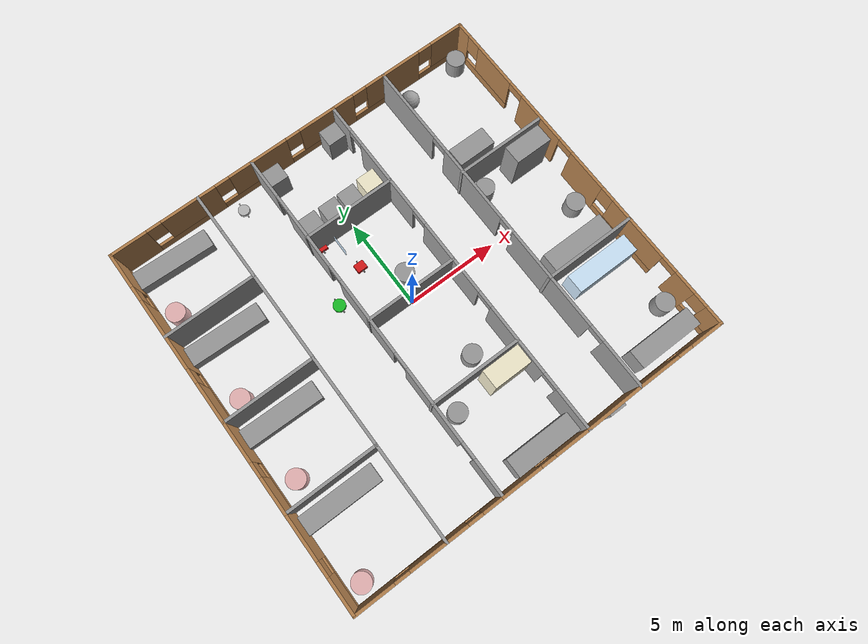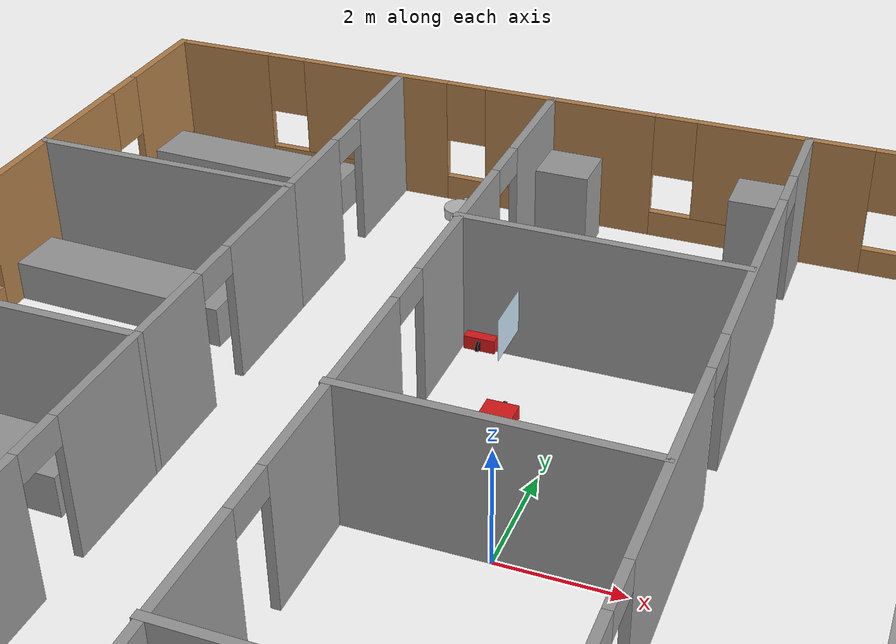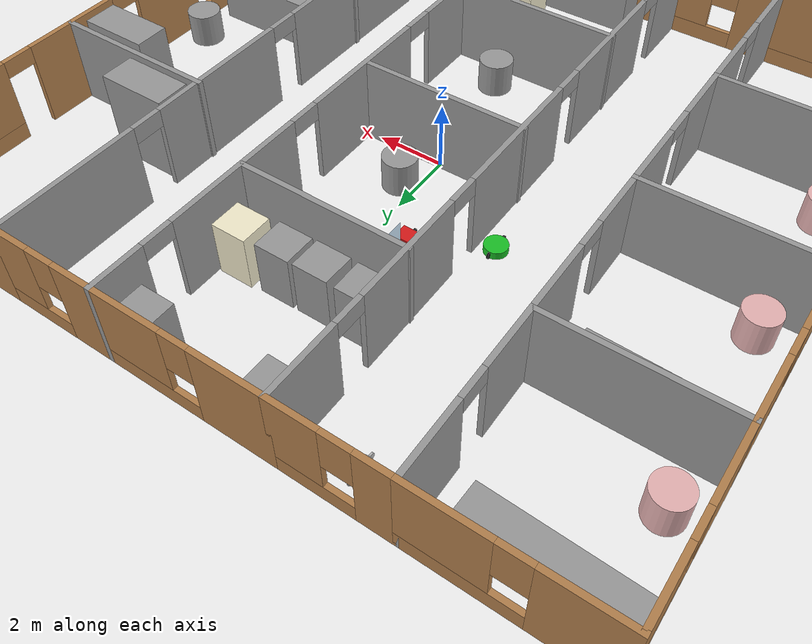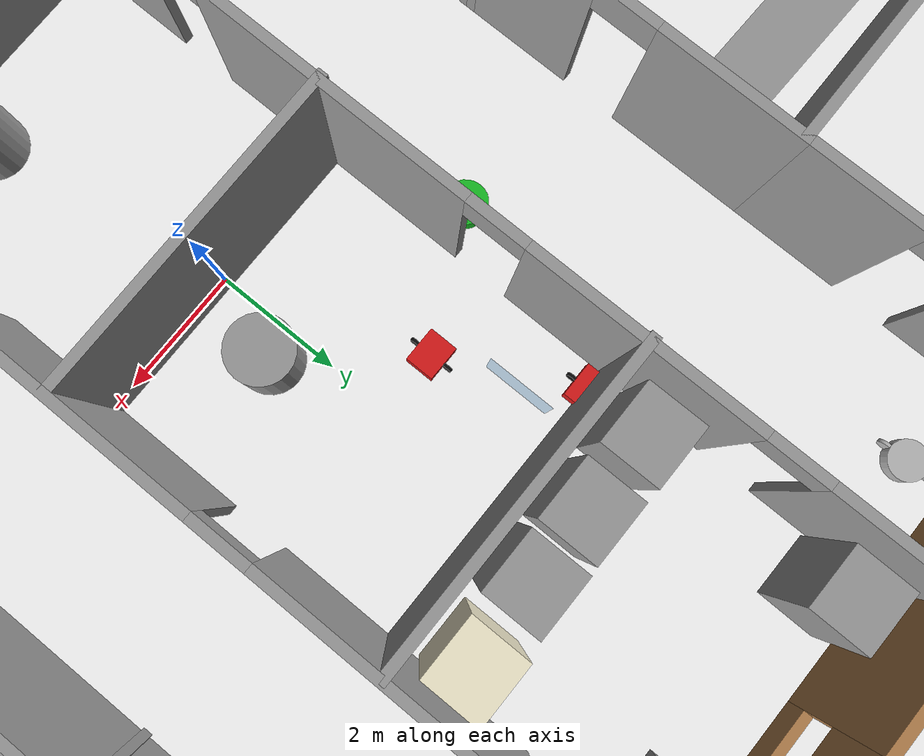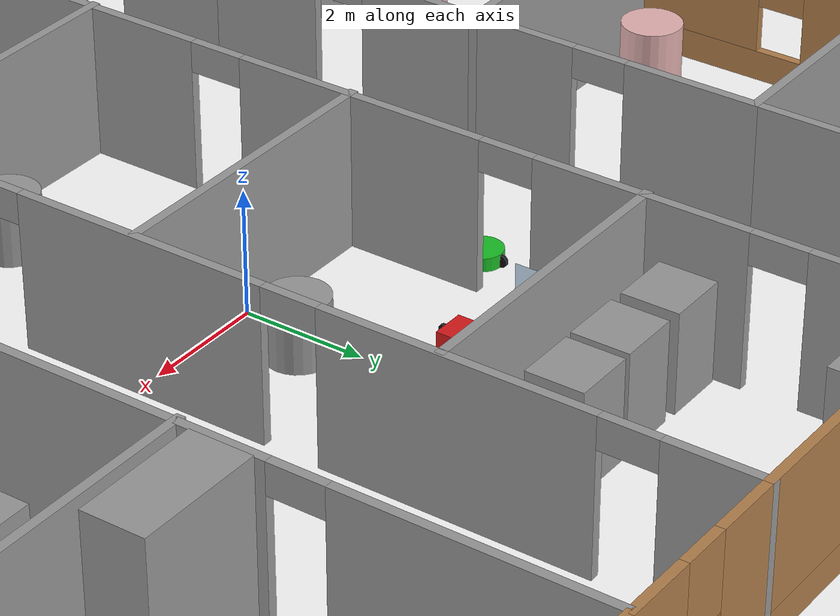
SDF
<sdf version="1.7">
 <world name="default">
  <plugin name="gazebo_ros_state" filename="libgazebo_ros_state.so"/>
  <plugin name="gazebo_ros_init" filename="libgazebo_ros_init.so"/>
  <plugin name="gazebo_ros_factory" filename="libgazebo_ros_factory.so"/>
  <light name="sun" type="directional">
   <pose>0 0 10 0 -0 0</pose>
   <diffuse>0.8 0.8 0.8 1</diffuse>
   <specular>0.2 0.2 0.2 1</specular>
   <attenuation>
    <range>1000</range>
    <constant>0.9</constant>
    <linear>0.01</linear>
    <quadratic>0.001</quadratic>
   </attenuation>
   <direction>-0.5 0.1 -0.9</direction>
   <spot><inner_angle>0</inner_angle><outer_angle>0</outer_angle><falloff>0</falloff></spot>
  </light>
  <model name="ground_plane">
   <static>1</static>
   <link name="link">
    <collision name="collision">
     <geometry><plane><normal>0 0 1</normal><size>100 100</size></plane></geometry>
     <surface><friction><ode><mu>100</mu><mu2>50</mu2></ode></friction></surface>
    </collision>
    <visual name="visual">
     <cast_shadows>0</cast_shadows>
     <geometry><plane><normal>0 0 1</normal><size>100 100</size></plane></geometry>
     <material>
      <script><uri>file://media/materials/scripts/gazebo.material</uri><name>Gazebo/Grey</name></script>
     </material>
    </visual>
   </link>
  </model>
  <gravity>0 0 -9.8</gravity>
  <magnetic_field>6e-06 2.3e-05 -4.2e-05</magnetic_field>
  <atmosphere type="adiabatic"/>
  <physics type="ode">
   <max_step_size>0.001</max_step_size>
   <real_time_factor>1</real_time_factor>
   <real_time_update_rate>1000</real_time_update_rate>
  </physics>
  <scene><ambient>0.4 0.4 0.4 1</ambient><background>0.7 0.7 0.7 1</background><shadows>1</shadows></scene>
  <audio><device>default</device></audio>
  <spherical_coordinates>
   <surface_model>EARTH_WGS84</surface_model>
   <latitude_deg>0</latitude_deg>
   <longitude_deg>0</longitude_deg>
   <elevation>0</elevation>
   <heading_deg>0</heading_deg>
  </spherical_coordinates>
  <light name="user_point_light_0" type="point">
   <pose>-13.5072 8.21606 1 0 -0 0</pose>
   <diffuse>0.5 0.5 0.5 1</diffuse>
   <specular>0.1 0.1 0.1 1</specular>
   <attenuation>
    <range>20</range>
    <constant>0.5</constant>
    <linear>0.01</linear>
    <quadratic>0.001</quadratic>
   </attenuation>
   <cast_shadows>0</cast_shadows>
   <direction>0 0 -1</direction>
   <spot><inner_angle>0</inner_angle><outer_angle>0</outer_angle><falloff>0</falloff></spot>
  </light>
  <light name="user_spot_light_0" type="spot">
   <pose>-2.66975 6.67026 1 0 -0 0</pose>
   <diffuse>0.5 0.5 0.5 1</diffuse>
   <specular>0.1 0.1 0.1 1</specular>
   <direction>0 0 -1</direction>
   <attenuation>
    <range>20</range>
    <constant>0.5</constant>
    <linear>0.01</linear>
    <quadratic>0.001</quadratic>
   </attenuation>
   <cast_shadows>0</cast_shadows>
   <spot><inner_angle>0.6</inner_angle><outer_angle>1</outer_angle><falloff>1</falloff></spot>
  </light>
  <model name="hospital_floor_v2">
   <link name="Door_19">
    <collision name="Door_19_Collision">
     <geometry><box><size>0.9 0.17 2</size></box></geometry>
     <pose>0 0 1 0 -0 0</pose>
    </collision>
    <visual name="Door_19_Visual">
     <pose>0 0 1 0 -0 0</pose>
     <geometry><box><size>0.9 0.17 2</size></box></geometry>
     <material>
      <script><uri>file://media/materials/scripts/gazebo.material</uri><name>Gazebo/Grey</name></script>
     </material>
    </visual>
    <pose>4.12711 -9.93446 0 0 -0 0</pose>
   </link>
   <link name="Wall_111">
    <pose>7.95 9.8256 0 0 -0 0</pose>
    <visual name="Wall_111_Visual_0">
     <pose>-1.37417 0 1.25 0 -0 0</pose>
     <geometry><box><size>2.25167 0.15 2.5</size></box></geometry>
     <material>
      <script><uri>file://media/materials/scripts/gazebo.material</uri><name>Gazebo/Wood</name></script>
      <ambient>1 1 1 1</ambient>
     </material>
     <meta><layer>0</layer></meta>
    </visual>
    <collision name="Wall_111_Collision_0">
     <geometry><box><size>2.25167 0.15 2.5</size></box></geometry>
     <pose>-1.37417 0 1.25 0 -0 0</pose>
    </collision>
    <visual name="Wall_111_Visual_1">
     <pose>1.12583 0 0.25 0 -0 0</pose>
     <geometry><box><size>2.74833 0.15 0.5</size></box></geometry>
     <material>
      <script><uri>file://media/materials/scripts/gazebo.material</uri><name>Gazebo/Wood</name></script>
      <ambient>1 1 1 1</ambient>
     </material>
     <meta><layer>0</layer></meta>
    </visual>
    <collision name="Wall_111_Collision_1">
     <geometry><box><size>2.74833 0.15 0.5</size></box></geometry>
     <pose>1.12583 0 0.25 0 -0 0</pose>
    </collision>
    <visual name="Wall_111_Visual_2">
     <pose>1.52583 0 1.5 0 -0 0</pose>
     <geometry><box><size>1.94833 0.15 2</size></box></geometry>
     <material>
      <script><uri>file://media/materials/scripts/gazebo.material</uri><name>Gazebo/Wood</name></script>
      <ambient>1 1 1 1</ambient>
     </material>
     <meta><layer>0</layer></meta>
    </visual>
    <collision name="Wall_111_Collision_2">
     <geometry><box><size>1.94833 0.15 2</size></box></geometry>
     <pose>1.52583 0 1.5 0 -0 0</pose>
    </collision>
    <visual name="Wall_111_Visual_3">
     <pose>0.151665 0 1.9 0 -0 0</pose>
     <geometry><box><size>0.8 0.15 1.2</size></box></geometry>
     <material>
      <script><uri>file://media/materials/scripts/gazebo.material</uri><name>Gazebo/Wood</name></script>
      <ambient>1 1 1 1</ambient>
     </material>
     <meta><layer>0</layer></meta>
    </visual>
    <collision name="Wall_111_Collision_3">
     <geometry><box><size>0.8 0.15 1.2</size></box></geometry>
     <pose>0.151665 0 1.9 0 -0 0</pose>
    </collision>
   </link>
   <link name="Wall_112">
    <pose>10.375 0.025599 0 0 -0 -1.5708</pose>
    <visual name="Wall_112_Visual_0">
     <pose>-9.42467 0 1.25 0 -0 0</pose>
     <geometry><box><size>0.900667 0.15 2.5</size></box></geometry>
     <material>
      <script><uri>file://media/materials/scripts/gazebo.material</uri><name>Gazebo/Wood</name></script>
      <ambient>1 1 1 1</ambient>
     </material>
     <meta><layer>0</layer></meta>
    </visual>
    <collision name="Wall_112_Collision_0">
     <geometry><box><size>0.900667 0.15 2.5</size></box></geometry>
     <pose>-9.42467 0 1.25 0 -0 0</pose>
    </collision>
    <visual name="Wall_112_Visual_1">
     <pose>-3.24113 0 1.25 0 -0 0</pose>
     <geometry><box><size>2.95288 0.15 2.5</size></box></geometry>
     <material>
      <script><uri>file://media/materials/scripts/gazebo.material</uri><name>Gazebo/Wood</name></script>
      <ambient>1 1 1 1</ambient>
     </material>
     <meta><layer>0</layer></meta>
    </visual>
    <collision name="Wall_112_Collision_1">
     <geometry><box><size>2.95288 0.15 2.5</size></box></geometry>
     <pose>-3.24113 0 1.25 0 -0 0</pose>
    </collision>
    <visual name="Wall_112_Visual_2">
     <pose>0.29202 0 1.25 0 -0 0</pose>
     <geometry><box><size>2.31342 0.15 2.5</size></box></geometry>
     <material>
      <script><uri>file://media/materials/scripts/gazebo.material</uri><name>Gazebo/Wood</name></script>
      <ambient>1 1 1 1</ambient>
     </material>
     <meta><layer>0</layer></meta>
    </visual>
    <collision name="Wall_112_Collision_2">
     <geometry><box><size>2.31342 0.15 2.5</size></box></geometry>
     <pose>0.29202 0 1.25 0 -0 0</pose>
    </collision>
    <visual name="Wall_112_Visual_3">
     <pose>7.36916 0 1.25 0 -0 0</pose>
     <geometry><box><size>1.2995 0.15 2.5</size></box></geometry>
     <material>
      <script><uri>file://media/materials/scripts/gazebo.material</uri><name>Gazebo/Wood</name></script>
      <ambient>1 1 1 1</ambient>
     </material>
     <meta><layer>0</layer></meta>
    </visual>
    <collision name="Wall_112_Collision_3">
     <geometry><box><size>1.2995 0.15 2.5</size></box></geometry>
     <pose>7.36916 0 1.25 0 -0 0</pose>
    </collision>
    <visual name="Wall_112_Visual_4">
     <pose>-7.29595 0 0.25 0 -0 0</pose>
     <geometry><box><size>3.35676 0.15 0.5</size></box></geometry>
     <material>
      <script><uri>file://media/materials/scripts/gazebo.material</uri><name>Gazebo/Wood</name></script>
      <ambient>1 1 1 1</ambient>
     </material>
     <meta><layer>0</layer></meta>
    </visual>
    <collision name="Wall_112_Collision_4">
     <geometry><box><size>3.35676 0.15 0.5</size></box></geometry>
     <pose>-7.29595 0 0.25 0 -0 0</pose>
    </collision>
    <visual name="Wall_112_Visual_5">
     <pose>3.63407 0 0.25 0 -0 0</pose>
     <geometry><box><size>4.37068 0.15 0.5</size></box></geometry>
     <material>
      <script><uri>file://media/materials/scripts/gazebo.material</uri><name>Gazebo/Wood</name></script>
      <ambient>1 1 1 1</ambient>
     </material>
     <meta><layer>0</layer></meta>
    </visual>
    <collision name="Wall_112_Collision_5">
     <geometry><box><size>4.37068 0.15 0.5</size></box></geometry>
     <pose>3.63407 0 0.25 0 -0 0</pose>
    </collision>
    <visual name="Wall_112_Visual_6">
     <pose>8.94696 0 0.25 0 -0 0</pose>
     <geometry><box><size>1.85609 0.15 0.5</size></box></geometry>
     <material>
      <script><uri>file://media/materials/scripts/gazebo.material</uri><name>Gazebo/Wood</name></script>
      <ambient>1 1 1 1</ambient>
     </material>
     <meta><layer>0</layer></meta>
    </visual>
    <collision name="Wall_112_Collision_6">
     <geometry><box><size>1.85609 0.15 0.5</size></box></geometry>
     <pose>8.94696 0 0.25 0 -0 0</pose>
    </collision>
    <visual name="Wall_112_Visual_7">
     <pose>-6.89595 0 1.5 0 -0 0</pose>
     <geometry><box><size>2.55676 0.15 2</size></box></geometry>
     <material>
      <script><uri>file://media/materials/scripts/gazebo.material</uri><name>Gazebo/Wood</name></script>
      <ambient>1 1 1 1</ambient>
     </material>
     <meta><layer>0</layer></meta>
    </visual>
    <collision name="Wall_112_Collision_7">
     <geometry><box><size>2.55676 0.15 2</size></box></geometry>
     <pose>-6.89595 0 1.5 0 -0 0</pose>
    </collision>
    <visual name="Wall_112_Visual_8">
     <pose>-6.89595 0 1.5 0 -0 0</pose>
     <geometry><box><size>2.55676 0.15 2</size></box></geometry>
     <material>
      <script><uri>file://media/materials/scripts/gazebo.material</uri><name>Gazebo/Wood</name></script>
      <ambient>1 1 1 1</ambient>
     </material>
     <meta><layer>0</layer></meta>
    </visual>
    <collision name="Wall_112_Collision_8">
     <geometry><box><size>2.55676 0.15 2</size></box></geometry>
     <pose>-6.89595 0 1.5 0 -0 0</pose>
    </collision>
    <visual name="Wall_112_Visual_9">
     <pose>4.03407 0 1.5 0 -0 0</pose>
     <geometry><box><size>3.57068 0.15 2</size></box></geometry>
     <material>
      <script><uri>file://media/materials/scripts/gazebo.material</uri><name>Gazebo/Wood</name></script>
      <ambient>1 1 1 1</ambient>
     </material>
     <meta><layer>0</layer></meta>
    </visual>
    <collision name="Wall_112_Collision_9">
     <geometry><box><size>3.57068 0.15 2</size></box></geometry>
     <pose>4.03407 0 1.5 0 -0 0</pose>
    </collision>
    <visual name="Wall_112_Visual_10">
     <pose>4.03407 0 1.5 0 -0 0</pose>
     <geometry><box><size>3.57068 0.15 2</size></box></geometry>
     <material>
      <script><uri>file://media/materials/scripts/gazebo.material</uri><name>Gazebo/Wood</name></script>
      <ambient>1 1 1 1</ambient>
     </material>
     <meta><layer>0</layer></meta>
    </visual>
    <collision name="Wall_112_Collision_10">
     <geometry><box><size>3.57068 0.15 2</size></box></geometry>
     <pose>4.03407 0 1.5 0 -0 0</pose>
    </collision>
    <visual name="Wall_112_Visual_11">
     <pose>9.34695 0 1.5 0 -0 0</pose>
     <geometry><box><size>1.05609 0.15 2</size></box></geometry>
     <material>
      <script><uri>file://media/materials/scripts/gazebo.material</uri><name>Gazebo/Wood</name></script>
      <ambient>1 1 1 1</ambient>
     </material>
     <meta><layer>0</layer></meta>
    </visual>
    <collision name="Wall_112_Collision_11">
     <geometry><box><size>1.05609 0.15 2</size></box></geometry>
     <pose>9.34695 0 1.5 0 -0 0</pose>
    </collision>
    <visual name="Wall_112_Visual_12">
     <pose>-8.57433 0 1.9 0 -0 0</pose>
     <geometry><box><size>0.8 0.15 1.2</size></box></geometry>
     <material>
      <script><uri>file://media/materials/scripts/gazebo.material</uri><name>Gazebo/Wood</name></script>
      <ambient>1 1 1 1</ambient>
     </material>
     <meta><layer>0</layer></meta>
    </visual>
    <collision name="Wall_112_Collision_12">
     <geometry><box><size>0.8 0.15 1.2</size></box></geometry>
     <pose>-8.57433 0 1.9 0 -0 0</pose>
    </collision>
    <visual name="Wall_112_Visual_13">
     <pose>1.84873 0 1.9 0 -0 0</pose>
     <geometry><box><size>0.8 0.15 1.2</size></box></geometry>
     <material>
      <script><uri>file://media/materials/scripts/gazebo.material</uri><name>Gazebo/Wood</name></script>
      <ambient>1 1 1 1</ambient>
     </material>
     <meta><layer>0</layer></meta>
    </visual>
    <collision name="Wall_112_Collision_13">
     <geometry><box><size>0.8 0.15 1.2</size></box></geometry>
     <pose>1.84873 0 1.9 0 -0 0</pose>
    </collision>
    <visual name="Wall_112_Visual_14">
     <pose>8.41891 0 1.9 0 -0 0</pose>
     <geometry><box><size>0.8 0.15 1.2</size></box></geometry>
     <material>
      <script><uri>file://media/materials/scripts/gazebo.material</uri><name>Gazebo/Wood</name></script>
      <ambient>1 1 1 1</ambient>
     </material>
     <meta><layer>0</layer></meta>
    </visual>
    <collision name="Wall_112_Collision_14">
     <geometry><box><size>0.8 0.15 1.2</size></box></geometry>
     <pose>8.41891 0 1.9 0 -0 0</pose>
    </collision>
    <visual name="Wall_112_Visual_15">
     <pose>-1.31469 0 2.25 0 -0 0</pose>
     <geometry><box><size>0.9 0.15 0.5</size></box></geometry>
     <material>
      <script><uri>file://media/materials/scripts/gazebo.material</uri><name>Gazebo/Wood</name></script>
      <ambient>1 1 1 1</ambient>
     </material>
     <meta><layer>0</layer></meta>
    </visual>
    <collision name="Wall_112_Collision_15">
     <geometry><box><size>0.9 0.15 0.5</size></box></geometry>
     <pose>-1.31469 0 2.25 0 -0 0</pose>
    </collision>
    <visual name="Wall_112_Visual_16">
     <pose>-5.16757 0 2.25 0 -0 0</pose>
     <geometry><box><size>0.9 0.15 0.5</size></box></geometry>
     <material>
      <script><uri>file://media/materials/scripts/gazebo.material</uri><name>Gazebo/Wood</name></script>
      <ambient>1 1 1 1</ambient>
     </material>
     <meta><layer>0</layer></meta>
    </visual>
    <collision name="Wall_112_Collision_16">
     <geometry><box><size>0.9 0.15 0.5</size></box></geometry>
     <pose>-5.16757 0 2.25 0 -0 0</pose>
    </collision>
    <visual name="Wall_112_Visual_17">
     <pose>-5.16757 0 2.25 0 -0 0</pose>
     <geometry><box><size>0.9 0.15 0.5</size></box></geometry>
     <material>
      <script><uri>file://media/materials/scripts/gazebo.material</uri><name>Gazebo/Wood</name></script>
      <ambient>1 1 1 1</ambient>
     </material>
     <meta><layer>0</layer></meta>
    </visual>
    <collision name="Wall_112_Collision_17">
     <geometry><box><size>0.9 0.15 0.5</size></box></geometry>
     <pose>-5.16757 0 2.25 0 -0 0</pose>
    </collision>
    <visual name="Wall_112_Visual_18">
     <pose>6.26941 0 2.25 0 -0 0</pose>
     <geometry><box><size>0.9 0.15 0.5</size></box></geometry>
     <material>
      <script><uri>file://media/materials/scripts/gazebo.material</uri><name>Gazebo/Wood</name></script>
      <ambient>1 1 1 1</ambient>
     </material>
     <meta><layer>0</layer></meta>
    </visual>
    <collision name="Wall_112_Collision_18">
     <geometry><box><size>0.9 0.15 0.5</size></box></geometry>
     <pose>6.26941 0 2.25 0 -0 0</pose>
    </collision>
    <visual name="Wall_112_Visual_19">
     <pose>6.26941 0 2.25 0 -0 0</pose>
     <geometry><box><size>0.9 0.15 0.5</size></box></geometry>
     <material>
      <script><uri>file://media/materials/scripts/gazebo.material</uri><name>Gazebo/Wood</name></script>
      <ambient>1 1 1 1</ambient>
     </material>
     <meta><layer>0</layer></meta>
    </visual>
    <collision name="Wall_112_Collision_19">
     <geometry><box><size>0.9 0.15 0.5</size></box></geometry>
     <pose>6.26941 0 2.25 0 -0 0</pose>
    </collision>
   </link>
   <link name="Wall_113">
    <pose>7.95 -9.7744 0 0 -0 3.14159</pose>
    <visual name="Wall_113_Visual_0">
     <pose>-1.56639 0 1.25 0 -0 0</pose>
     <geometry><box><size>1.86722 0.15 2.5</size></box></geometry>
     <material>
      <script><uri>file://media/materials/scripts/gazebo.material</uri><name>Gazebo/Wood</name></script>
      <ambient>1 1 1 1</ambient>
     </material>
     <meta><layer>0</layer></meta>
    </visual>
    <collision name="Wall_113_Collision_0">
     <geometry><box><size>1.86722 0.15 2.5</size></box></geometry>
     <pose>-1.56639 0 1.25 0 -0 0</pose>
    </collision>
    <visual name="Wall_113_Visual_1">
     <pose>0.933611 0 0.25 0 -0 0</pose>
     <geometry><box><size>3.13278 0.15 0.5</size></box></geometry>
     <material>
      <script><uri>file://media/materials/scripts/gazebo.material</uri><name>Gazebo/Wood</name></script>
      <ambient>1 1 1 1</ambient>
     </material>
     <meta><layer>0</layer></meta>
    </visual>
    <collision name="Wall_113_Collision_1">
     <geometry><box><size>3.13278 0.15 0.5</size></box></geometry>
     <pose>0.933611 0 0.25 0 -0 0</pose>
    </collision>
    <visual name="Wall_113_Visual_2">
     <pose>1.33361 0 1.5 0 -0 0</pose>
     <geometry><box><size>2.33278 0.15 2</size></box></geometry>
     <material>
      <script><uri>file://media/materials/scripts/gazebo.material</uri><name>Gazebo/Wood</name></script>
      <ambient>1 1 1 1</ambient>
     </material>
     <meta><layer>0</layer></meta>
    </visual>
    <collision name="Wall_113_Collision_2">
     <geometry><box><size>2.33278 0.15 2</size></box></geometry>
     <pose>1.33361 0 1.5 0 -0 0</pose>
    </collision>
    <visual name="Wall_113_Visual_3">
     <pose>-0.232779 0 1.9 0 -0 0</pose>
     <geometry><box><size>0.8 0.15 1.2</size></box></geometry>
     <material>
      <script><uri>file://media/materials/scripts/gazebo.material</uri><name>Gazebo/Wood</name></script>
      <ambient>1 1 1 1</ambient>
     </material>
     <meta><layer>0</layer></meta>
    </visual>
    <collision name="Wall_113_Collision_3">
     <geometry><box><size>0.8 0.15 1.2</size></box></geometry>
     <pose>-0.232779 0 1.9 0 -0 0</pose>
    </collision>
   </link>
   <link name="Wall_115">
    <collision name="Wall_115_Collision">
     <geometry><box><size>5 0.15 2.5</size></box></geometry>
     <pose>0 0 1.25 0 -0 0</pose>
    </collision>
    <visual name="Wall_115_Visual">
     <pose>0 0 1.25 0 -0 0</pose>
     <geometry><box><size>5 0.15 2.5</size></box></geometry>
     <material>
      <script><uri>file://media/materials/scripts/gazebo.material</uri><name>Gazebo/Grey</name></script>
      <ambient>1 1 1 1</ambient>
     </material>
     <meta><layer>0</layer></meta>
    </visual>
    <pose>-0.036828 5.04089 0 0 -0 0</pose>
   </link>
   <link name="Wall_117">
    <collision name="Wall_117_Collision">
     <geometry><box><size>5 0.15 2.5</size></box></geometry>
     <pose>0 0 1.25 0 -0 0</pose>
    </collision>
    <visual name="Wall_117_Visual">
     <pose>0 0 1.25 0 -0 0</pose>
     <geometry><box><size>5 0.15 2.5</size></box></geometry>
     <material>
      <script><uri>file://media/materials/scripts/gazebo.material</uri><name>Gazebo/Grey</name></script>
      <ambient>1 1 1 1</ambient>
     </material>
     <meta><layer>0</layer></meta>
    </visual>
    <pose>-0.036828 0.052719 0 0 -0 0</pose>
   </link>
   <link name="Wall_119">
    <collision name="Wall_119_Collision">
     <geometry><box><size>5 0.15 2.5</size></box></geometry>
     <pose>0 0 1.25 0 -0 0</pose>
    </collision>
    <visual name="Wall_119_Visual">
     <pose>0 0 1.25 0 -0 0</pose>
     <geometry><box><size>5 0.15 2.5</size></box></geometry>
     <material>
      <script><uri>file://media/materials/scripts/gazebo.material</uri><name>Gazebo/Grey</name></script>
      <ambient>1 1 1 1</ambient>
     </material>
     <meta><layer>0</layer></meta>
    </visual>
    <pose>-0.036828 -4.77454 0 0 -0 0</pose>
   </link>
   <link name="Wall_123">
    <collision name="Wall_123_Collision">
     <geometry><box><size>5 0.15 2.5</size></box></geometry>
     <pose>0 0 1.25 0 -0 0</pose>
    </collision>
    <visual name="Wall_123_Visual">
     <pose>0 0 1.25 0 -0 0</pose>
     <geometry><box><size>5 0.15 2.5</size></box></geometry>
     <material>
      <script><uri>file://media/materials/scripts/gazebo.material</uri><name>Gazebo/Grey</name></script>
      <ambient>1 1 1 1</ambient>
     </material>
     <meta><layer>0</layer></meta>
    </visual>
    <pose>7.90133 3.27089 0 0 -0 0</pose>
   </link>
   <link name="Wall_125">
    <collision name="Wall_125_Collision">
     <geometry><box><size>5 0.15 2.5</size></box></geometry>
     <pose>0 0 1.25 0 -0 0</pose>
    </collision>
    <visual name="Wall_125_Visual">
     <pose>0 0 1.25 0 -0 0</pose>
     <geometry><box><size>5 0.15 2.5</size></box></geometry>
     <material>
      <script><uri>file://media/materials/scripts/gazebo.material</uri><name>Gazebo/Grey</name></script>
      <ambient>1 1 1 1</ambient>
     </material>
     <meta><layer>0</layer></meta>
    </visual>
    <pose>7.90133 -3.38 0 0 -0 0</pose>
   </link>
   <link name="Wall_24">
    <pose>-10.375 2.5506 0 0 -0 -1.5708</pose>
    <visual name="Wall_24_Visual_0">
     <pose>-1.53431 0 1.25 0 -0 0</pose>
     <geometry><box><size>1.93138 0.15 2.5</size></box></geometry>
     <material>
      <script><uri>file://media/materials/scripts/gazebo.material</uri><name>Gazebo/Wood</name></script>
      <ambient>1 1 1 1</ambient>
     </material>
     <meta><layer>0</layer></meta>
    </visual>
    <collision name="Wall_24_Collision_0">
     <geometry><box><size>1.93138 0.15 2.5</size></box></geometry>
     <pose>-1.53431 0 1.25 0 -0 0</pose>
    </collision>
    <visual name="Wall_24_Visual_1">
     <pose>0.965692 0 0.25 0 -0 0</pose>
     <geometry><box><size>3.06862 0.15 0.5</size></box></geometry>
     <material>
      <script><uri>file://media/materials/scripts/gazebo.material</uri><name>Gazebo/Wood</name></script>
      <ambient>1 1 1 1</ambient>
     </material>
     <meta><layer>0</layer></meta>
    </visual>
    <collision name="Wall_24_Collision_1">
     <geometry><box><size>3.06862 0.15 0.5</size></box></geometry>
     <pose>0.965692 0 0.25 0 -0 0</pose>
    </collision>
    <visual name="Wall_24_Visual_2">
     <pose>1.36569 0 1.5 0 -0 0</pose>
     <geometry><box><size>2.26862 0.15 2</size></box></geometry>
     <material>
      <script><uri>file://media/materials/scripts/gazebo.material</uri><name>Gazebo/Wood</name></script>
      <ambient>1 1 1 1</ambient>
     </material>
     <meta><layer>0</layer></meta>
    </visual>
    <collision name="Wall_24_Collision_2">
     <geometry><box><size>2.26862 0.15 2</size></box></geometry>
     <pose>1.36569 0 1.5 0 -0 0</pose>
    </collision>
    <visual name="Wall_24_Visual_3">
     <pose>-0.168617 0 1.9 0 -0 0</pose>
     <geometry><box><size>0.8 0.15 1.2</size></box></geometry>
     <material>
      <script><uri>file://media/materials/scripts/gazebo.material</uri><name>Gazebo/Wood</name></script>
      <ambient>1 1 1 1</ambient>
     </material>
     <meta><layer>0</layer></meta>
    </visual>
    <collision name="Wall_24_Collision_3">
     <geometry><box><size>0.8 0.15 1.2</size></box></geometry>
     <pose>-0.168617 0 1.9 0 -0 0</pose>
    </collision>
   </link>
   <link name="Wall_28">
    <collision name="Wall_28_Collision">
     <geometry><box><size>5 0.15 2.5</size></box></geometry>
     <pose>0 0 1.25 0 -0 0</pose>
    </collision>
    <visual name="Wall_28_Visual">
     <pose>0 0 1.25 0 -0 0</pose>
     <geometry><box><size>5 0.15 2.5</size></box></geometry>
     <material>
      <script><uri>file://media/materials/scripts/gazebo.material</uri><name>Gazebo/Grey</name></script>
      <ambient>1 1 1 1</ambient>
     </material>
     <meta><layer>0</layer></meta>
    </visual>
    <pose>-7.95 4.9756 0 0 -0 0</pose>
   </link>
   <link name="Wall_29">
    <pose>-5.525 2.5506 0 0 -0 -1.5708</pose>
    <visual name="Wall_29_Visual_0">
     <pose>-1.3768 0 1.25 0 -0 0</pose>
     <geometry><box><size>2.24639 0.15 2.5</size></box></geometry>
     <material>
      <script><uri>file://media/materials/scripts/gazebo.material</uri><name>Gazebo/Grey</name></script>
      <ambient>1 1 1 1</ambient>
     </material>
     <meta><layer>0</layer></meta>
    </visual>
    <collision name="Wall_29_Collision_0">
     <geometry><box><size>2.24639 0.15 2.5</size></box></geometry>
     <pose>-1.3768 0 1.25 0 -0 0</pose>
    </collision>
    <visual name="Wall_29_Visual_1">
     <pose>1.5732 0 1.25 0 -0 0</pose>
     <geometry><box><size>1.85361 0.15 2.5</size></box></geometry>
     <material>
      <script><uri>file://media/materials/scripts/gazebo.material</uri><name>Gazebo/Grey</name></script>
      <ambient>1 1 1 1</ambient>
     </material>
     <meta><layer>0</layer></meta>
    </visual>
    <collision name="Wall_29_Collision_1">
     <geometry><box><size>1.85361 0.15 2.5</size></box></geometry>
     <pose>1.5732 0 1.25 0 -0 0</pose>
    </collision>
    <visual name="Wall_29_Visual_2">
     <pose>0.196393 0 2.25 0 -0 0</pose>
     <geometry><box><size>0.9 0.15 0.5</size></box></geometry>
     <material>
      <script><uri>file://media/materials/scripts/gazebo.material</uri><name>Gazebo/Grey</name></script>
      <ambient>1 1 1 1</ambient>
     </material>
     <meta><layer>0</layer></meta>
    </visual>
    <collision name="Wall_29_Collision_2">
     <geometry><box><size>0.9 0.15 0.5</size></box></geometry>
     <pose>0.196393 0 2.25 0 -0 0</pose>
    </collision>
   </link>
   <link name="Wall_30">
    <collision name="Wall_30_Collision">
     <geometry><box><size>5 0.15 2.5</size></box></geometry>
     <pose>0 0 1.25 0 -0 0</pose>
    </collision>
    <visual name="Wall_30_Visual">
     <pose>0 0 1.25 0 -0 0</pose>
     <geometry><box><size>5 0.15 2.5</size></box></geometry>
     <material>
      <script><uri>file://media/materials/scripts/gazebo.material</uri><name>Gazebo/Grey</name></script>
      <ambient>1 1 1 1</ambient>
     </material>
     <meta><layer>0</layer></meta>
    </visual>
    <pose>-7.95 0.125599 0 0 -0 3.14159</pose>
   </link>
   <link name="Wall_31">
    <pose>-10.375 -2.2994 0 0 -0 -1.5708</pose>
    <visual name="Wall_31_Visual_0">
     <pose>-1.38396 0 1.25 0 -0 0</pose>
     <geometry><box><size>2.23208 0.15 2.5</size></box></geometry>
     <material>
      <script><uri>file://media/materials/scripts/gazebo.material</uri><name>Gazebo/Wood</name></script>
      <ambient>1 1 1 1</ambient>
     </material>
     <meta><layer>0</layer></meta>
    </visual>
    <collision name="Wall_31_Collision_0">
     <geometry><box><size>2.23208 0.15 2.5</size></box></geometry>
     <pose>-1.38396 0 1.25 0 -0 0</pose>
    </collision>
    <visual name="Wall_31_Visual_1">
     <pose>1.11604 0 0.25 0 -0 0</pose>
     <geometry><box><size>2.76792 0.15 0.5</size></box></geometry>
     <material>
      <script><uri>file://media/materials/scripts/gazebo.material</uri><name>Gazebo/Wood</name></script>
      <ambient>1 1 1 1</ambient>
     </material>
     <meta><layer>0</layer></meta>
    </visual>
    <collision name="Wall_31_Collision_1">
     <geometry><box><size>2.76792 0.15 0.5</size></box></geometry>
     <pose>1.11604 0 0.25 0 -0 0</pose>
    </collision>
    <visual name="Wall_31_Visual_2">
     <pose>1.51604 0 1.5 0 -0 0</pose>
     <geometry><box><size>1.96792 0.15 2</size></box></geometry>
     <material>
      <script><uri>file://media/materials/scripts/gazebo.material</uri><name>Gazebo/Wood</name></script>
      <ambient>1 1 1 1</ambient>
     </material>
     <meta><layer>0</layer></meta>
    </visual>
    <collision name="Wall_31_Collision_2">
     <geometry><box><size>1.96792 0.15 2</size></box></geometry>
     <pose>1.51604 0 1.5 0 -0 0</pose>
    </collision>
    <visual name="Wall_31_Visual_3">
     <pose>0.13208 0 1.9 0 -0 0</pose>
     <geometry><box><size>0.8 0.15 1.2</size></box></geometry>
     <material>
      <script><uri>file://media/materials/scripts/gazebo.material</uri><name>Gazebo/Wood</name></script>
      <ambient>1 1 1 1</ambient>
     </material>
     <meta><layer>0</layer></meta>
    </visual>
    <collision name="Wall_31_Collision_3">
     <geometry><box><size>0.8 0.15 1.2</size></box></geometry>
     <pose>0.13208 0 1.9 0 -0 0</pose>
    </collision>
   </link>
   <link name="Wall_32">
    <collision name="Wall_32_Collision">
     <geometry><box><size>5 0.15 2.5</size></box></geometry>
     <pose>0 0 1.25 0 -0 0</pose>
    </collision>
    <visual name="Wall_32_Visual">
     <pose>0 0 1.25 0 -0 0</pose>
     <geometry><box><size>5 0.15 2.5</size></box></geometry>
     <material>
      <script><uri>file://media/materials/scripts/gazebo.material</uri><name>Gazebo/Grey</name></script>
      <ambient>1 1 1 1</ambient>
     </material>
     <meta><layer>0</layer></meta>
    </visual>
    <pose>-7.95 -4.7244 0 0 -0 0</pose>
   </link>
   <link name="Wall_33">
    <pose>-5.525 -2.2994 0 0 -0 1.5708</pose>
    <visual name="Wall_33_Visual_0">
     <pose>-1.52076 0 1.25 0 -0 0</pose>
     <geometry><box><size>1.95848 0.15 2.5</size></box></geometry>
     <material>
      <script><uri>file://media/materials/scripts/gazebo.material</uri><name>Gazebo/Grey</name></script>
      <ambient>1 1 1 1</ambient>
     </material>
     <meta><layer>0</layer></meta>
    </visual>
    <collision name="Wall_33_Collision_0">
     <geometry><box><size>1.95848 0.15 2.5</size></box></geometry>
     <pose>-1.52076 0 1.25 0 -0 0</pose>
    </collision>
    <visual name="Wall_33_Visual_1">
     <pose>1.42924 0 1.25 0 -0 0</pose>
     <geometry><box><size>2.14152 0.15 2.5</size></box></geometry>
     <material>
      <script><uri>file://media/materials/scripts/gazebo.material</uri><name>Gazebo/Grey</name></script>
      <ambient>1 1 1 1</ambient>
     </material>
     <meta><layer>0</layer></meta>
    </visual>
    <collision name="Wall_33_Collision_1">
     <geometry><box><size>2.14152 0.15 2.5</size></box></geometry>
     <pose>1.42924 0 1.25 0 -0 0</pose>
    </collision>
    <visual name="Wall_33_Visual_2">
     <pose>-0.091523 0 2.25 0 -0 0</pose>
     <geometry><box><size>0.9 0.15 0.5</size></box></geometry>
     <material>
      <script><uri>file://media/materials/scripts/gazebo.material</uri><name>Gazebo/Grey</name></script>
      <ambient>1 1 1 1</ambient>
     </material>
     <meta><layer>0</layer></meta>
    </visual>
    <collision name="Wall_33_Collision_2">
     <geometry><box><size>0.9 0.15 0.5</size></box></geometry>
     <pose>-0.091523 0 2.25 0 -0 0</pose>
    </collision>
   </link>
   <link name="Wall_35">
    <pose>-10.375 -7.2744 0 0 -0 -1.5708</pose>
    <visual name="Wall_35_Visual_0">
     <pose>-1.37889 0 1.25 0 -0 0</pose>
     <geometry><box><size>2.49222 0.15 2.5</size></box></geometry>
     <material>
      <script><uri>file://media/materials/scripts/gazebo.material</uri><name>Gazebo/Wood</name></script>
      <ambient>1 1 1 1</ambient>
     </material>
     <meta><layer>0</layer></meta>
    </visual>
    <collision name="Wall_35_Collision_0">
     <geometry><box><size>2.49222 0.15 2.5</size></box></geometry>
     <pose>-1.37889 0 1.25 0 -0 0</pose>
    </collision>
    <visual name="Wall_35_Visual_1">
     <pose>1.24611 0 0.25 0 -0 0</pose>
     <geometry><box><size>2.75778 0.15 0.5</size></box></geometry>
     <material>
      <script><uri>file://media/materials/scripts/gazebo.material</uri><name>Gazebo/Wood</name></script>
      <ambient>1 1 1 1</ambient>
     </material>
     <meta><layer>0</layer></meta>
    </visual>
    <collision name="Wall_35_Collision_1">
     <geometry><box><size>2.75778 0.15 0.5</size></box></geometry>
     <pose>1.24611 0 0.25 0 -0 0</pose>
    </collision>
    <visual name="Wall_35_Visual_2">
     <pose>1.64611 0 1.5 0 -0 0</pose>
     <geometry><box><size>1.95778 0.15 2</size></box></geometry>
     <material>
      <script><uri>file://media/materials/scripts/gazebo.material</uri><name>Gazebo/Wood</name></script>
      <ambient>1 1 1 1</ambient>
     </material>
     <meta><layer>0</layer></meta>
    </visual>
    <collision name="Wall_35_Collision_2">
     <geometry><box><size>1.95778 0.15 2</size></box></geometry>
     <pose>1.64611 0 1.5 0 -0 0</pose>
    </collision>
    <visual name="Wall_35_Visual_3">
     <pose>0.26722 0 1.9 0 -0 0</pose>
     <geometry><box><size>0.8 0.15 1.2</size></box></geometry>
     <material>
      <script><uri>file://media/materials/scripts/gazebo.material</uri><name>Gazebo/Wood</name></script>
      <ambient>1 1 1 1</ambient>
     </material>
     <meta><layer>0</layer></meta>
    </visual>
    <collision name="Wall_35_Collision_3">
     <geometry><box><size>0.8 0.15 1.2</size></box></geometry>
     <pose>0.26722 0 1.9 0 -0 0</pose>
    </collision>
   </link>
   <link name="Wall_36">
    <pose>-7.95 -9.8244 0 0 -0 0</pose>
    <visual name="Wall_36_Visual_0">
     <pose>-1.41383 0 1.25 0 -0 0</pose>
     <geometry><box><size>2.17234 0.15 2.5</size></box></geometry>
     <material>
      <script><uri>file://media/materials/scripts/gazebo.material</uri><name>Gazebo/Wood</name></script>
      <ambient>1 1 1 1</ambient>
     </material>
     <meta><layer>0</layer></meta>
    </visual>
    <collision name="Wall_36_Collision_0">
     <geometry><box><size>2.17234 0.15 2.5</size></box></geometry>
     <pose>-1.41383 0 1.25 0 -0 0</pose>
    </collision>
    <visual name="Wall_36_Visual_1">
     <pose>1.08617 0 0.25 0 -0 0</pose>
     <geometry><box><size>2.82766 0.15 0.5</size></box></geometry>
     <material>
      <script><uri>file://media/materials/scripts/gazebo.material</uri><name>Gazebo/Wood</name></script>
      <ambient>1 1 1 1</ambient>
     </material>
     <meta><layer>0</layer></meta>
    </visual>
    <collision name="Wall_36_Collision_1">
     <geometry><box><size>2.82766 0.15 0.5</size></box></geometry>
     <pose>1.08617 0 0.25 0 -0 0</pose>
    </collision>
    <visual name="Wall_36_Visual_2">
     <pose>1.48617 0 1.5 0 -0 0</pose>
     <geometry><box><size>2.02766 0.15 2</size></box></geometry>
     <material>
      <script><uri>file://media/materials/scripts/gazebo.material</uri><name>Gazebo/Wood</name></script>
      <ambient>1 1 1 1</ambient>
     </material>
     <meta><layer>0</layer></meta>
    </visual>
    <collision name="Wall_36_Collision_2">
     <geometry><box><size>2.02766 0.15 2</size></box></geometry>
     <pose>1.48617 0 1.5 0 -0 0</pose>
    </collision>
    <visual name="Wall_36_Visual_3">
     <pose>0.072339 0 1.9 0 -0 0</pose>
     <geometry><box><size>0.8 0.15 1.2</size></box></geometry>
     <material>
      <script><uri>file://media/materials/scripts/gazebo.material</uri><name>Gazebo/Wood</name></script>
      <ambient>1 1 1 1</ambient>
     </material>
     <meta><layer>0</layer></meta>
    </visual>
    <collision name="Wall_36_Collision_3">
     <geometry><box><size>0.8 0.15 1.2</size></box></geometry>
     <pose>0.072339 0 1.9 0 -0 0</pose>
    </collision>
   </link>
   <link name="Wall_37">
    <pose>-5.525 -7.2744 0 0 -0 1.5708</pose>
    <visual name="Wall_37_Visual_0">
     <pose>-1.50888 0 1.25 0 -0 0</pose>
     <geometry><box><size>2.23223 0.15 2.5</size></box></geometry>
     <material>
      <script><uri>file://media/materials/scripts/gazebo.material</uri><name>Gazebo/Grey</name></script>
      <ambient>1 1 1 1</ambient>
     </material>
     <meta><layer>0</layer></meta>
    </visual>
    <collision name="Wall_37_Collision_0">
     <geometry><box><size>2.23223 0.15 2.5</size></box></geometry>
     <pose>-1.50888 0 1.25 0 -0 0</pose>
    </collision>
    <visual name="Wall_37_Visual_1">
     <pose>1.56612 0 1.25 0 -0 0</pose>
     <geometry><box><size>2.11777 0.15 2.5</size></box></geometry>
     <material>
      <script><uri>file://media/materials/scripts/gazebo.material</uri><name>Gazebo/Grey</name></script>
      <ambient>1 1 1 1</ambient>
     </material>
     <meta><layer>0</layer></meta>
    </visual>
    <collision name="Wall_37_Collision_1">
     <geometry><box><size>2.11777 0.15 2.5</size></box></geometry>
     <pose>1.56612 0 1.25 0 -0 0</pose>
    </collision>
    <visual name="Wall_37_Visual_2">
     <pose>0.057233 0 2.25 0 -0 0</pose>
     <geometry><box><size>0.9 0.15 0.5</size></box></geometry>
     <material>
      <script><uri>file://media/materials/scripts/gazebo.material</uri><name>Gazebo/Grey</name></script>
      <ambient>1 1 1 1</ambient>
     </material>
     <meta><layer>0</layer></meta>
    </visual>
    <collision name="Wall_37_Collision_2">
     <geometry><box><size>0.9 0.15 0.5</size></box></geometry>
     <pose>0.057233 0 2.25 0 -0 0</pose>
    </collision>
   </link>
   <link name="Wall_39">
    <pose>-10.375 7.4006 0 0 -0 1.5708</pose>
    <visual name="Wall_39_Visual_0">
     <pose>-1.39785 0 1.25 0 -0 0</pose>
     <geometry><box><size>2.2043 0.15 2.5</size></box></geometry>
     <material>
      <script><uri>file://media/materials/scripts/gazebo.material</uri><name>Gazebo/Wood</name></script>
      <ambient>1 1 1 1</ambient>
     </material>
     <meta><layer>0</layer></meta>
    </visual>
    <collision name="Wall_39_Collision_0">
     <geometry><box><size>2.2043 0.15 2.5</size></box></geometry>
     <pose>-1.39785 0 1.25 0 -0 0</pose>
    </collision>
    <visual name="Wall_39_Visual_1">
     <pose>1.10215 0 0.25 0 -0 0</pose>
     <geometry><box><size>2.7957 0.15 0.5</size></box></geometry>
     <material>
      <script><uri>file://media/materials/scripts/gazebo.material</uri><name>Gazebo/Wood</name></script>
      <ambient>1 1 1 1</ambient>
     </material>
     <meta><layer>0</layer></meta>
    </visual>
    <collision name="Wall_39_Collision_1">
     <geometry><box><size>2.7957 0.15 0.5</size></box></geometry>
     <pose>1.10215 0 0.25 0 -0 0</pose>
    </collision>
    <visual name="Wall_39_Visual_2">
     <pose>1.50215 0 1.5 0 -0 0</pose>
     <geometry><box><size>1.9957 0.15 2</size></box></geometry>
     <material>
      <script><uri>file://media/materials/scripts/gazebo.material</uri><name>Gazebo/Wood</name></script>
      <ambient>1 1 1 1</ambient>
     </material>
     <meta><layer>0</layer></meta>
    </visual>
    <collision name="Wall_39_Collision_2">
     <geometry><box><size>1.9957 0.15 2</size></box></geometry>
     <pose>1.50215 0 1.5 0 -0 0</pose>
    </collision>
    <visual name="Wall_39_Visual_3">
     <pose>0.104303 0 1.9 0 -0 0</pose>
     <geometry><box><size>0.8 0.15 1.2</size></box></geometry>
     <material>
      <script><uri>file://media/materials/scripts/gazebo.material</uri><name>Gazebo/Wood</name></script>
      <ambient>1 1 1 1</ambient>
     </material>
     <meta><layer>0</layer></meta>
    </visual>
    <collision name="Wall_39_Collision_3">
     <geometry><box><size>0.8 0.15 1.2</size></box></geometry>
     <pose>0.104303 0 1.9 0 -0 0</pose>
    </collision>
   </link>
   <link name="Wall_40">
    <pose>-7.95 9.8256 0 0 -0 0</pose>
    <visual name="Wall_40_Visual_0">
     <pose>-1.47467 0 1.25 0 -0 0</pose>
     <geometry><box><size>2.05067 0.15 2.5</size></box></geometry>
     <material>
      <script><uri>file://media/materials/scripts/gazebo.material</uri><name>Gazebo/Wood</name></script>
      <ambient>1 1 1 1</ambient>
     </material>
     <meta><layer>0</layer></meta>
    </visual>
    <collision name="Wall_40_Collision_0">
     <geometry><box><size>2.05067 0.15 2.5</size></box></geometry>
     <pose>-1.47467 0 1.25 0 -0 0</pose>
    </collision>
    <visual name="Wall_40_Visual_1">
     <pose>1.02533 0 0.25 0 -0 0</pose>
     <geometry><box><size>2.94933 0.15 0.5</size></box></geometry>
     <material>
      <script><uri>file://media/materials/scripts/gazebo.material</uri><name>Gazebo/Wood</name></script>
      <ambient>1 1 1 1</ambient>
     </material>
     <meta><layer>0</layer></meta>
    </visual>
    <collision name="Wall_40_Collision_1">
     <geometry><box><size>2.94933 0.15 0.5</size></box></geometry>
     <pose>1.02533 0 0.25 0 -0 0</pose>
    </collision>
    <visual name="Wall_40_Visual_2">
     <pose>1.42533 0 1.5 0 -0 0</pose>
     <geometry><box><size>2.14933 0.15 2</size></box></geometry>
     <material>
      <script><uri>file://media/materials/scripts/gazebo.material</uri><name>Gazebo/Wood</name></script>
      <ambient>1 1 1 1</ambient>
     </material>
     <meta><layer>0</layer></meta>
    </visual>
    <collision name="Wall_40_Collision_2">
     <geometry><box><size>2.14933 0.15 2</size></box></geometry>
     <pose>1.42533 0 1.5 0 -0 0</pose>
    </collision>
    <visual name="Wall_40_Visual_3">
     <pose>-0.049332 0 1.9 0 -0 0</pose>
     <geometry><box><size>0.8 0.15 1.2</size></box></geometry>
     <material>
      <script><uri>file://media/materials/scripts/gazebo.material</uri><name>Gazebo/Wood</name></script>
      <ambient>1 1 1 1</ambient>
     </material>
     <meta><layer>0</layer></meta>
    </visual>
    <collision name="Wall_40_Collision_3">
     <geometry><box><size>0.8 0.15 1.2</size></box></geometry>
     <pose>-0.049332 0 1.9 0 -0 0</pose>
    </collision>
   </link>
   <link name="Wall_41">
    <pose>-5.525 7.4006 0 0 -0 -1.5708</pose>
    <visual name="Wall_41_Visual_0">
     <pose>-1.40548 0 1.25 0 -0 0</pose>
     <geometry><box><size>2.18904 0.15 2.5</size></box></geometry>
     <material>
      <script><uri>file://media/materials/scripts/gazebo.material</uri><name>Gazebo/Grey</name></script>
      <ambient>1 1 1 1</ambient>
     </material>
     <meta><layer>0</layer></meta>
    </visual>
    <collision name="Wall_41_Collision_0">
     <geometry><box><size>2.18904 0.15 2.5</size></box></geometry>
     <pose>-1.40548 0 1.25 0 -0 0</pose>
    </collision>
    <visual name="Wall_41_Visual_1">
     <pose>1.54452 0 1.25 0 -0 0</pose>
     <geometry><box><size>1.91096 0.15 2.5</size></box></geometry>
     <material>
      <script><uri>file://media/materials/scripts/gazebo.material</uri><name>Gazebo/Grey</name></script>
      <ambient>1 1 1 1</ambient>
     </material>
     <meta><layer>0</layer></meta>
    </visual>
    <collision name="Wall_41_Collision_1">
     <geometry><box><size>1.91096 0.15 2.5</size></box></geometry>
     <pose>1.54452 0 1.25 0 -0 0</pose>
    </collision>
    <visual name="Wall_41_Visual_2">
     <pose>0.139037 0 2.25 0 -0 0</pose>
     <geometry><box><size>0.9 0.15 0.5</size></box></geometry>
     <material>
      <script><uri>file://media/materials/scripts/gazebo.material</uri><name>Gazebo/Grey</name></script>
      <ambient>1 1 1 1</ambient>
     </material>
     <meta><layer>0</layer></meta>
    </visual>
    <collision name="Wall_41_Collision_2">
     <geometry><box><size>0.9 0.15 0.5</size></box></geometry>
     <pose>0.139037 0 2.25 0 -0 0</pose>
    </collision>
   </link>
   <link name="Wall_43">
    <pose>-3.975 9.8256 0 0 -0 0</pose>
    <visual name="Wall_43_Visual_0">
     <pose>-1.09822 0 1.25 0 -0 0</pose>
     <geometry><box><size>1.05355 0.15 2.5</size></box></geometry>
     <material>
      <script><uri>file://media/materials/scripts/gazebo.material</uri><name>Gazebo/Wood</name></script>
      <ambient>1 1 1 1</ambient>
     </material>
     <meta><layer>0</layer></meta>
    </visual>
    <collision name="Wall_43_Collision_0">
     <geometry><box><size>1.05355 0.15 2.5</size></box></geometry>
     <pose>-1.09822 0 1.25 0 -0 0</pose>
    </collision>
    <visual name="Wall_43_Visual_1">
     <pose>0.526776 0 0.25 0 -0 0</pose>
     <geometry><box><size>2.19645 0.15 0.5</size></box></geometry>
     <material>
      <script><uri>file://media/materials/scripts/gazebo.material</uri><name>Gazebo/Wood</name></script>
      <ambient>1 1 1 1</ambient>
     </material>
     <meta><layer>0</layer></meta>
    </visual>
    <collision name="Wall_43_Collision_1">
     <geometry><box><size>2.19645 0.15 0.5</size></box></geometry>
     <pose>0.526776 0 0.25 0 -0 0</pose>
    </collision>
    <visual name="Wall_43_Visual_2">
     <pose>0.926776 0 1.5 0 -0 0</pose>
     <geometry><box><size>1.39645 0.15 2</size></box></geometry>
     <material>
      <script><uri>file://media/materials/scripts/gazebo.material</uri><name>Gazebo/Wood</name></script>
      <ambient>1 1 1 1</ambient>
     </material>
     <meta><layer>0</layer></meta>
    </visual>
    <collision name="Wall_43_Collision_2">
     <geometry><box><size>1.39645 0.15 2</size></box></geometry>
     <pose>0.926776 0 1.5 0 -0 0</pose>
    </collision>
    <visual name="Wall_43_Visual_3">
     <pose>-0.171448 0 1.9 0 -0 0</pose>
     <geometry><box><size>0.8 0.15 1.2</size></box></geometry>
     <material>
      <script><uri>file://media/materials/scripts/gazebo.material</uri><name>Gazebo/Wood</name></script>
      <ambient>1 1 1 1</ambient>
     </material>
     <meta><layer>0</layer></meta>
    </visual>
    <collision name="Wall_43_Collision_3">
     <geometry><box><size>0.8 0.15 1.2</size></box></geometry>
     <pose>-0.171448 0 1.9 0 -0 0</pose>
    </collision>
   </link>
   <link name="Wall_44">
    <pose>-2.425 0.025599 0 0 -0 -1.5708</pose>
    <visual name="Wall_44_Visual_0">
     <pose>-8.73992 0 1.25 0 -0 0</pose>
     <geometry><box><size>2.27015 0.15 2.5</size></box></geometry>
     <material>
      <script><uri>file://media/materials/scripts/gazebo.material</uri><name>Gazebo/Grey</name></script>
      <ambient>1 1 1 1</ambient>
     </material>
     <meta><layer>0</layer></meta>
    </visual>
    <collision name="Wall_44_Collision_0">
     <geometry><box><size>2.27015 0.15 2.5</size></box></geometry>
     <pose>-8.73992 0 1.25 0 -0 0</pose>
    </collision>
    <visual name="Wall_44_Visual_1">
     <pose>-4.96479 0 1.25 0 -0 0</pose>
     <geometry><box><size>3.48012 0.15 2.5</size></box></geometry>
     <material>
      <script><uri>file://media/materials/scripts/gazebo.material</uri><name>Gazebo/Grey</name></script>
      <ambient>1 1 1 1</ambient>
     </material>
     <meta><layer>0</layer></meta>
    </visual>
    <collision name="Wall_44_Collision_1">
     <geometry><box><size>3.48012 0.15 2.5</size></box></geometry>
     <pose>-4.96479 0 1.25 0 -0 0</pose>
    </collision>
    <visual name="Wall_44_Visual_2">
     <pose>-0.199382 0 1.25 0 -0 0</pose>
     <geometry><box><size>4.2507 0.15 2.5</size></box></geometry>
     <material>
      <script><uri>file://media/materials/scripts/gazebo.material</uri><name>Gazebo/Grey</name></script>
      <ambient>1 1 1 1</ambient>
     </material>
     <meta><layer>0</layer></meta>
    </visual>
    <collision name="Wall_44_Collision_2">
     <geometry><box><size>4.2507 0.15 2.5</size></box></geometry>
     <pose>-0.199382 0 1.25 0 -0 0</pose>
    </collision>
    <visual name="Wall_44_Visual_3">
     <pose>4.8702 0 1.25 0 -0 0</pose>
     <geometry><box><size>4.08847 0.15 2.5</size></box></geometry>
     <material>
      <script><uri>file://media/materials/scripts/gazebo.material</uri><name>Gazebo/Grey</name></script>
      <ambient>1 1 1 1</ambient>
     </material>
     <meta><layer>0</layer></meta>
    </visual>
    <collision name="Wall_44_Collision_3">
     <geometry><box><size>4.08847 0.15 2.5</size></box></geometry>
     <pose>4.8702 0 1.25 0 -0 0</pose>
    </collision>
    <visual name="Wall_44_Visual_4">
     <pose>8.84472 0 1.25 0 -0 0</pose>
     <geometry><box><size>2.06056 0.15 2.5</size></box></geometry>
     <material>
      <script><uri>file://media/materials/scripts/gazebo.material</uri><name>Gazebo/Grey</name></script>
      <ambient>1 1 1 1</ambient>
     </material>
     <meta><layer>0</layer></meta>
    </visual>
    <collision name="Wall_44_Collision_4">
     <geometry><box><size>2.06056 0.15 2.5</size></box></geometry>
     <pose>8.84472 0 1.25 0 -0 0</pose>
    </collision>
    <visual name="Wall_44_Visual_5">
     <pose>-7.15485 0 2.25 0 -0 0</pose>
     <geometry><box><size>0.9 0.15 0.5</size></box></geometry>
     <material>
      <script><uri>file://media/materials/scripts/gazebo.material</uri><name>Gazebo/Grey</name></script>
      <ambient>1 1 1 1</ambient>
     </material>
     <meta><layer>0</layer></meta>
    </visual>
    <collision name="Wall_44_Collision_5">
     <geometry><box><size>0.9 0.15 0.5</size></box></geometry>
     <pose>-7.15485 0 2.25 0 -0 0</pose>
    </collision>
    <visual name="Wall_44_Visual_6">
     <pose>-2.77473 0 2.25 0 -0 0</pose>
     <geometry><box><size>0.9 0.15 0.5</size></box></geometry>
     <material>
      <script><uri>file://media/materials/scripts/gazebo.material</uri><name>Gazebo/Grey</name></script>
      <ambient>1 1 1 1</ambient>
     </material>
     <meta><layer>0</layer></meta>
    </visual>
    <collision name="Wall_44_Collision_6">
     <geometry><box><size>0.9 0.15 0.5</size></box></geometry>
     <pose>-2.77473 0 2.25 0 -0 0</pose>
    </collision>
    <visual name="Wall_44_Visual_7">
     <pose>2.37597 0 2.25 0 -0 0</pose>
     <geometry><box><size>0.9 0.15 0.5</size></box></geometry>
     <material>
      <script><uri>file://media/materials/scripts/gazebo.material</uri><name>Gazebo/Grey</name></script>
      <ambient>1 1 1 1</ambient>
     </material>
     <meta><layer>0</layer></meta>
    </visual>
    <collision name="Wall_44_Collision_7">
     <geometry><box><size>0.9 0.15 0.5</size></box></geometry>
     <pose>2.37597 0 2.25 0 -0 0</pose>
    </collision>
    <visual name="Wall_44_Visual_8">
     <pose>7.36444 0 2.25 0 -0 0</pose>
     <geometry><box><size>0.9 0.15 0.5</size></box></geometry>
     <material>
      <script><uri>file://media/materials/scripts/gazebo.material</uri><name>Gazebo/Grey</name></script>
      <ambient>1 1 1 1</ambient>
     </material>
     <meta><layer>0</layer></meta>
    </visual>
    <collision name="Wall_44_Collision_8">
     <geometry><box><size>0.9 0.15 0.5</size></box></geometry>
     <pose>7.36444 0 2.25 0 -0 0</pose>
    </collision>
   </link>
   <link name="Wall_47">
    <pose>-3.975 -9.8244 0 0 -0 0</pose>
    <visual name="Wall_47_Visual_0">
     <pose>-0.996933 0 1.25 0 -0 0</pose>
     <geometry><box><size>1.25654 0.15 2.5</size></box></geometry>
     <material>
      <script><uri>file://media/materials/scripts/gazebo.material</uri><name>Gazebo/Wood</name></script>
      <ambient>1 1 1 1</ambient>
     </material>
     <meta><layer>0</layer></meta>
    </visual>
    <collision name="Wall_47_Collision_0">
     <geometry><box><size>1.25654 0.15 2.5</size></box></geometry>
     <pose>-0.996933 0 1.25 0 -0 0</pose>
    </collision>
    <visual name="Wall_47_Visual_1">
     <pose>0.628268 0 0.25 0 -0 0</pose>
     <geometry><box><size>1.99387 0.15 0.5</size></box></geometry>
     <material>
      <script><uri>file://media/materials/scripts/gazebo.material</uri><name>Gazebo/Wood</name></script>
      <ambient>1 1 1 1</ambient>
     </material>
     <meta><layer>0</layer></meta>
    </visual>
    <collision name="Wall_47_Collision_1">
     <geometry><box><size>1.99387 0.15 0.5</size></box></geometry>
     <pose>0.628268 0 0.25 0 -0 0</pose>
    </collision>
    <visual name="Wall_47_Visual_2">
     <pose>1.02827 0 1.5 0 -0 0</pose>
     <geometry><box><size>1.19387 0.15 2</size></box></geometry>
     <material>
      <script><uri>file://media/materials/scripts/gazebo.material</uri><name>Gazebo/Wood</name></script>
      <ambient>1 1 1 1</ambient>
     </material>
     <meta><layer>0</layer></meta>
    </visual>
    <collision name="Wall_47_Collision_2">
     <geometry><box><size>1.19387 0.15 2</size></box></geometry>
     <pose>1.02827 0 1.5 0 -0 0</pose>
    </collision>
    <visual name="Wall_47_Visual_3">
     <pose>0.031335 0 1.9 0 -0 0</pose>
     <geometry><box><size>0.8 0.15 1.2</size></box></geometry>
     <material>
      <script><uri>file://media/materials/scripts/gazebo.material</uri><name>Gazebo/Wood</name></script>
      <ambient>1 1 1 1</ambient>
     </material>
     <meta><layer>0</layer></meta>
    </visual>
    <collision name="Wall_47_Collision_3">
     <geometry><box><size>0.8 0.15 1.2</size></box></geometry>
     <pose>0.031335 0 1.9 0 -0 0</pose>
    </collision>
   </link>
   <link name="Wall_51">
    <pose>0 9.8256 0 0 -0 0</pose>
    <visual name="Wall_51_Visual_0">
     <pose>-1.45483 0 1.25 0 -0 0</pose>
     <geometry><box><size>2.09033 0.15 2.5</size></box></geometry>
     <material>
      <script><uri>file://media/materials/scripts/gazebo.material</uri><name>Gazebo/Wood</name></script>
      <ambient>1 1 1 1</ambient>
     </material>
     <meta><layer>0</layer></meta>
    </visual>
    <collision name="Wall_51_Collision_0">
     <geometry><box><size>2.09033 0.15 2.5</size></box></geometry>
     <pose>-1.45483 0 1.25 0 -0 0</pose>
    </collision>
    <visual name="Wall_51_Visual_1">
     <pose>1.04517 0 0.25 0 -0 0</pose>
     <geometry><box><size>2.90967 0.15 0.5</size></box></geometry>
     <material>
      <script><uri>file://media/materials/scripts/gazebo.material</uri><name>Gazebo/Wood</name></script>
      <ambient>1 1 1 1</ambient>
     </material>
     <meta><layer>0</layer></meta>
    </visual>
    <collision name="Wall_51_Collision_1">
     <geometry><box><size>2.90967 0.15 0.5</size></box></geometry>
     <pose>1.04517 0 0.25 0 -0 0</pose>
    </collision>
    <visual name="Wall_51_Visual_2">
     <pose>1.44517 0 1.5 0 -0 0</pose>
     <geometry><box><size>2.10967 0.15 2</size></box></geometry>
     <material>
      <script><uri>file://media/materials/scripts/gazebo.material</uri><name>Gazebo/Wood</name></script>
      <ambient>1 1 1 1</ambient>
     </material>
     <meta><layer>0</layer></meta>
    </visual>
    <collision name="Wall_51_Collision_2">
     <geometry><box><size>2.10967 0.15 2</size></box></geometry>
     <pose>1.44517 0 1.5 0 -0 0</pose>
    </collision>
    <visual name="Wall_51_Visual_3">
     <pose>-0.009668 0 1.9 0 -0 0</pose>
     <geometry><box><size>0.8 0.15 1.2</size></box></geometry>
     <material>
      <script><uri>file://media/materials/scripts/gazebo.material</uri><name>Gazebo/Wood</name></script>
      <ambient>1 1 1 1</ambient>
     </material>
     <meta><layer>0</layer></meta>
    </visual>
    <collision name="Wall_51_Collision_3">
     <geometry><box><size>0.8 0.15 1.2</size></box></geometry>
     <pose>-0.009668 0 1.9 0 -0 0</pose>
    </collision>
   </link>
   <link name="Wall_60">
    <pose>0 -9.8244 0 0 -0 0</pose>
    <visual name="Wall_60_Visual_0">
     <pose>-1.394 0 1.25 0 -0 0</pose>
     <geometry><box><size>2.212 0.15 2.5</size></box></geometry>
     <material>
      <script><uri>file://media/materials/scripts/gazebo.material</uri><name>Gazebo/Wood</name></script>
      <ambient>1 1 1 1</ambient>
     </material>
     <meta><layer>0</layer></meta>
    </visual>
    <collision name="Wall_60_Collision_0">
     <geometry><box><size>2.212 0.15 2.5</size></box></geometry>
     <pose>-1.394 0 1.25 0 -0 0</pose>
    </collision>
    <visual name="Wall_60_Visual_1">
     <pose>1.106 0 0.25 0 -0 0</pose>
     <geometry><box><size>2.788 0.15 0.5</size></box></geometry>
     <material>
      <script><uri>file://media/materials/scripts/gazebo.material</uri><name>Gazebo/Wood</name></script>
      <ambient>1 1 1 1</ambient>
     </material>
     <meta><layer>0</layer></meta>
    </visual>
    <collision name="Wall_60_Collision_1">
     <geometry><box><size>2.788 0.15 0.5</size></box></geometry>
     <pose>1.106 0 0.25 0 -0 0</pose>
    </collision>
    <visual name="Wall_60_Visual_2">
     <pose>1.506 0 1.5 0 -0 0</pose>
     <geometry><box><size>1.988 0.15 2</size></box></geometry>
     <material>
      <script><uri>file://media/materials/scripts/gazebo.material</uri><name>Gazebo/Wood</name></script>
      <ambient>1 1 1 1</ambient>
     </material>
     <meta><layer>0</layer></meta>
    </visual>
    <collision name="Wall_60_Collision_2">
     <geometry><box><size>1.988 0.15 2</size></box></geometry>
     <pose>1.506 0 1.5 0 -0 0</pose>
    </collision>
    <visual name="Wall_60_Visual_3">
     <pose>0.112002 0 1.9 0 -0 0</pose>
     <geometry><box><size>0.8 0.15 1.2</size></box></geometry>
     <material>
      <script><uri>file://media/materials/scripts/gazebo.material</uri><name>Gazebo/Wood</name></script>
      <ambient>1 1 1 1</ambient>
     </material>
     <meta><layer>0</layer></meta>
    </visual>
    <collision name="Wall_60_Collision_3">
     <geometry><box><size>0.8 0.15 1.2</size></box></geometry>
     <pose>0.112002 0 1.9 0 -0 0</pose>
    </collision>
   </link>
   <link name="Wall_62">
    <pose>2.425 0.000599 0 0 -0 1.5708</pose>
    <visual name="Wall_62_Visual_0">
     <pose>-8.74333 0 1.25 0 -0 0</pose>
     <geometry><box><size>2.31335 0.15 2.5</size></box></geometry>
     <material>
      <script><uri>file://media/materials/scripts/gazebo.material</uri><name>Gazebo/Grey</name></script>
      <ambient>1 1 1 1</ambient>
     </material>
     <meta><layer>0</layer></meta>
    </visual>
    <collision name="Wall_62_Collision_0">
     <geometry><box><size>2.31335 0.15 2.5</size></box></geometry>
     <pose>-8.74333 0 1.25 0 -0 0</pose>
    </collision>
    <visual name="Wall_62_Visual_1">
     <pose>-4.76409 0 1.25 0 -0 0</pose>
     <geometry><box><size>3.84513 0.15 2.5</size></box></geometry>
     <material>
      <script><uri>file://media/materials/scripts/gazebo.material</uri><name>Gazebo/Grey</name></script>
      <ambient>1 1 1 1</ambient>
     </material>
     <meta><layer>0</layer></meta>
    </visual>
    <collision name="Wall_62_Collision_1">
     <geometry><box><size>3.84513 0.15 2.5</size></box></geometry>
     <pose>-4.76409 0 1.25 0 -0 0</pose>
    </collision>
    <visual name="Wall_62_Visual_2">
     <pose>0.143268 0 1.25 0 -0 0</pose>
     <geometry><box><size>4.16958 0.15 2.5</size></box></geometry>
     <material>
      <script><uri>file://media/materials/scripts/gazebo.material</uri><name>Gazebo/Grey</name></script>
      <ambient>1 1 1 1</ambient>
     </material>
     <meta><layer>0</layer></meta>
    </visual>
    <collision name="Wall_62_Collision_2">
     <geometry><box><size>4.16958 0.15 2.5</size></box></geometry>
     <pose>0.143268 0 1.25 0 -0 0</pose>
    </collision>
    <visual name="Wall_62_Visual_3">
     <pose>5.27369 0 1.25 0 -0 0</pose>
     <geometry><box><size>4.29125 0.15 2.5</size></box></geometry>
     <material>
      <script><uri>file://media/materials/scripts/gazebo.material</uri><name>Gazebo/Grey</name></script>
      <ambient>1 1 1 1</ambient>
     </material>
     <meta><layer>0</layer></meta>
    </visual>
    <collision name="Wall_62_Collision_3">
     <geometry><box><size>4.29125 0.15 2.5</size></box></geometry>
     <pose>5.27369 0 1.25 0 -0 0</pose>
    </collision>
    <visual name="Wall_62_Visual_4">
     <pose>9.10966 0 1.25 0 -0 0</pose>
     <geometry><box><size>1.58069 0.15 2.5</size></box></geometry>
     <material>
      <script><uri>file://media/materials/scripts/gazebo.material</uri><name>Gazebo/Grey</name></script>
      <ambient>1 1 1 1</ambient>
     </material>
     <meta><layer>0</layer></meta>
    </visual>
    <collision name="Wall_62_Collision_4">
     <geometry><box><size>1.58069 0.15 2.5</size></box></geometry>
     <pose>9.10966 0 1.25 0 -0 0</pose>
    </collision>
    <visual name="Wall_62_Visual_5">
     <pose>-7.13665 0 2.25 0 -0 0</pose>
     <geometry><box><size>0.9 0.15 0.5</size></box></geometry>
     <material>
      <script><uri>file://media/materials/scripts/gazebo.material</uri><name>Gazebo/Grey</name></script>
      <ambient>1 1 1 1</ambient>
     </material>
     <meta><layer>0</layer></meta>
    </visual>
    <collision name="Wall_62_Collision_5">
     <geometry><box><size>0.9 0.15 0.5</size></box></geometry>
     <pose>-7.13665 0 2.25 0 -0 0</pose>
    </collision>
    <visual name="Wall_62_Visual_6">
     <pose>-2.39152 0 2.25 0 -0 0</pose>
     <geometry><box><size>0.9 0.15 0.5</size></box></geometry>
     <material>
      <script><uri>file://media/materials/scripts/gazebo.material</uri><name>Gazebo/Grey</name></script>
      <ambient>1 1 1 1</ambient>
     </material>
     <meta><layer>0</layer></meta>
    </visual>
    <collision name="Wall_62_Collision_6">
     <geometry><box><size>0.9 0.15 0.5</size></box></geometry>
     <pose>-2.39152 0 2.25 0 -0 0</pose>
    </collision>
    <visual name="Wall_62_Visual_7">
     <pose>2.67806 0 2.25 0 -0 0</pose>
     <geometry><box><size>0.9 0.15 0.5</size></box></geometry>
     <material>
      <script><uri>file://media/materials/scripts/gazebo.material</uri><name>Gazebo/Grey</name></script>
      <ambient>1 1 1 1</ambient>
     </material>
     <meta><layer>0</layer></meta>
    </visual>
    <collision name="Wall_62_Collision_7">
     <geometry><box><size>0.9 0.15 0.5</size></box></geometry>
     <pose>2.67806 0 2.25 0 -0 0</pose>
    </collision>
    <visual name="Wall_62_Visual_8">
     <pose>7.86931 0 2.25 0 -0 0</pose>
     <geometry><box><size>0.9 0.15 0.5</size></box></geometry>
     <material>
      <script><uri>file://media/materials/scripts/gazebo.material</uri><name>Gazebo/Grey</name></script>
      <ambient>1 1 1 1</ambient>
     </material>
     <meta><layer>0</layer></meta>
    </visual>
    <collision name="Wall_62_Collision_8">
     <geometry><box><size>0.9 0.15 0.5</size></box></geometry>
     <pose>7.86931 0 2.25 0 -0 0</pose>
    </collision>
   </link>
   <link name="Wall_63">
    <pose>3.975 9.8256 0 0 -0 0</pose>
    <visual name="Wall_63_Visual_0">
     <pose>-0.997279 0 1.25 0 -0 0</pose>
     <geometry><box><size>1.25544 0.15 2.5</size></box></geometry>
     <material>
      <script><uri>file://media/materials/scripts/gazebo.material</uri><name>Gazebo/Wood</name></script>
      <ambient>1 1 1 1</ambient>
     </material>
     <meta><layer>0</layer></meta>
    </visual>
    <collision name="Wall_63_Collision_0">
     <geometry><box><size>1.25544 0.15 2.5</size></box></geometry>
     <pose>-0.997279 0 1.25 0 -0 0</pose>
    </collision>
    <visual name="Wall_63_Visual_1">
     <pose>0.627721 0 0.25 0 -0 0</pose>
     <geometry><box><size>1.99456 0.15 0.5</size></box></geometry>
     <material>
      <script><uri>file://media/materials/scripts/gazebo.material</uri><name>Gazebo/Wood</name></script>
      <ambient>1 1 1 1</ambient>
     </material>
     <meta><layer>0</layer></meta>
    </visual>
    <collision name="Wall_63_Collision_1">
     <geometry><box><size>1.99456 0.15 0.5</size></box></geometry>
     <pose>0.627721 0 0.25 0 -0 0</pose>
    </collision>
    <visual name="Wall_63_Visual_2">
     <pose>1.02772 0 1.5 0 -0 0</pose>
     <geometry><box><size>1.19456 0.15 2</size></box></geometry>
     <material>
      <script><uri>file://media/materials/scripts/gazebo.material</uri><name>Gazebo/Wood</name></script>
      <ambient>1 1 1 1</ambient>
     </material>
     <meta><layer>0</layer></meta>
    </visual>
    <collision name="Wall_63_Collision_2">
     <geometry><box><size>1.19456 0.15 2</size></box></geometry>
     <pose>1.02772 0 1.5 0 -0 0</pose>
    </collision>
    <visual name="Wall_63_Visual_3">
     <pose>0.030442 0 1.9 0 -0 0</pose>
     <geometry><box><size>0.8 0.15 1.2</size></box></geometry>
     <material>
      <script><uri>file://media/materials/scripts/gazebo.material</uri><name>Gazebo/Wood</name></script>
      <ambient>1 1 1 1</ambient>
     </material>
     <meta><layer>0</layer></meta>
    </visual>
    <collision name="Wall_63_Collision_3">
     <geometry><box><size>0.8 0.15 1.2</size></box></geometry>
     <pose>0.030442 0 1.9 0 -0 0</pose>
    </collision>
   </link>
   <link name="Wall_64">
    <pose>5.525 0.025599 0 0 -0 -1.5708</pose>
    <visual name="Wall_64_Visual_0">
     <pose>-7.72601 0 1.25 0 -0 0</pose>
     <geometry><box><size>4.29798 0.15 2.5</size></box></geometry>
     <material>
      <script><uri>file://media/materials/scripts/gazebo.material</uri><name>Gazebo/Grey</name></script>
      <ambient>1 1 1 1</ambient>
     </material>
     <meta><layer>0</layer></meta>
    </visual>
    <collision name="Wall_64_Collision_0">
     <geometry><box><size>4.29798 0.15 2.5</size></box></geometry>
     <pose>-7.72601 0 1.25 0 -0 0</pose>
    </collision>
    <visual name="Wall_64_Visual_1">
     <pose>-2.47056 0 1.25 0 -0 0</pose>
     <geometry><box><size>4.41292 0.15 2.5</size></box></geometry>
     <material>
      <script><uri>file://media/materials/scripts/gazebo.material</uri><name>Gazebo/Grey</name></script>
      <ambient>1 1 1 1</ambient>
     </material>
     <meta><layer>0</layer></meta>
    </visual>
    <collision name="Wall_64_Collision_1">
     <geometry><box><size>4.41292 0.15 2.5</size></box></geometry>
     <pose>-2.47056 0 1.25 0 -0 0</pose>
    </collision>
    <visual name="Wall_64_Visual_2">
     <pose>3.471 0 1.25 0 -0 0</pose>
     <geometry><box><size>5.67018 0.15 2.5</size></box></geometry>
     <material>
      <script><uri>file://media/materials/scripts/gazebo.material</uri><name>Gazebo/Grey</name></script>
      <ambient>1 1 1 1</ambient>
     </material>
     <meta><layer>0</layer></meta>
    </visual>
    <collision name="Wall_64_Collision_2">
     <geometry><box><size>5.67018 0.15 2.5</size></box></geometry>
     <pose>3.471 0 1.25 0 -0 0</pose>
    </collision>
    <visual name="Wall_64_Visual_3">
     <pose>8.54054 0 1.25 0 -0 0</pose>
     <geometry><box><size>2.66891 0.15 2.5</size></box></geometry>
     <material>
      <script><uri>file://media/materials/scripts/gazebo.material</uri><name>Gazebo/Grey</name></script>
      <ambient>1 1 1 1</ambient>
     </material>
     <meta><layer>0</layer></meta>
    </visual>
    <collision name="Wall_64_Collision_3">
     <geometry><box><size>2.66891 0.15 2.5</size></box></geometry>
     <pose>8.54054 0 1.25 0 -0 0</pose>
    </collision>
    <visual name="Wall_64_Visual_4">
     <pose>-5.12702 0 2.25 0 -0 0</pose>
     <geometry><box><size>0.9 0.15 0.5</size></box></geometry>
     <material>
      <script><uri>file://media/materials/scripts/gazebo.material</uri><name>Gazebo/Grey</name></script>
      <ambient>1 1 1 1</ambient>
     </material>
     <meta><layer>0</layer></meta>
    </visual>
    <collision name="Wall_64_Collision_4">
     <geometry><box><size>0.9 0.15 0.5</size></box></geometry>
     <pose>-5.12702 0 2.25 0 -0 0</pose>
    </collision>
    <visual name="Wall_64_Visual_5">
     <pose>0.185907 0 2.25 0 -0 0</pose>
     <geometry><box><size>0.9 0.15 0.5</size></box></geometry>
     <material>
      <script><uri>file://media/materials/scripts/gazebo.material</uri><name>Gazebo/Grey</name></script>
      <ambient>1 1 1 1</ambient>
     </material>
     <meta><layer>0</layer></meta>
    </visual>
    <collision name="Wall_64_Collision_5">
     <geometry><box><size>0.9 0.15 0.5</size></box></geometry>
     <pose>0.185907 0 2.25 0 -0 0</pose>
    </collision>
    <visual name="Wall_64_Visual_6">
     <pose>6.75609 0 2.25 0 -0 0</pose>
     <geometry><box><size>0.9 0.15 0.5</size></box></geometry>
     <material>
      <script><uri>file://media/materials/scripts/gazebo.material</uri><name>Gazebo/Grey</name></script>
      <ambient>1 1 1 1</ambient>
     </material>
     <meta><layer>0</layer></meta>
    </visual>
    <collision name="Wall_64_Collision_6">
     <geometry><box><size>0.9 0.15 0.5</size></box></geometry>
     <pose>6.75609 0 2.25 0 -0 0</pose>
    </collision>
   </link>
   <link name="Wall_65">
    <collision name="Wall_65_Collision">
     <geometry><box><size>3.2504 0.15 2.5</size></box></geometry>
     <pose>0 0 1.25 0 -0 0</pose>
    </collision>
    <visual name="Wall_65_Visual">
     <pose>0 0 1.25 0 -0 0</pose>
     <geometry><box><size>3.2504 0.15 2.5</size></box></geometry>
     <material>
      <script><uri>file://media/materials/scripts/gazebo.material</uri><name>Gazebo/Wood</name></script>
      <ambient>1 1 1 1</ambient>
     </material>
     <meta><layer>0</layer></meta>
    </visual>
    <pose>3.975 -9.7994 0 0 -0 -3.12547</pose>
   </link>
   <static>1</static>
  </model>
  <model name="unit_box_2">
   <pose>-0.346182 -0.620085 -110010 1e-06 4e-06 -3e-05</pose>
   <link name="link">
    <inertial>
     <mass>1</mass>
     <inertia>
      <ixx>0.166667</ixx>
      <ixy>0</ixy>
      <ixz>0</ixz>
      <iyy>0.166667</iyy>
      <iyz>0</iyz>
      <izz>0.166667</izz>
     </inertia>
    </inertial>
    <collision name="collision"><geometry><box><size>0 1 0.200347</size></box></geometry></collision>
    <visual name="visual">
     <geometry><box><size>0 1 0.200347</size></box></geometry>
     <material>
      <script><name>Gazebo/Grey</name><uri>file://media/materials/scripts/gazebo.material</uri></script>
     </material>
    </visual>
   </link>
  </model>
  <model name="unit_cylinder_0">
   <pose>0.63341 -3.89741 0.499994 -4e-06 -1e-06 0</pose>
   <link name="link">
    <inertial>
     <mass>1</mass>
     <inertia><ixx>0.145833</ixx><ixy>0</ixy><ixz>0</ixz><iyy>0.145833</iyy><iyz>0</iyz><izz>0.125</izz></inertia>
    </inertial>
    <collision name="collision">
     <geometry><cylinder><radius>0.5</radius><length>1</length></cylinder></geometry>
    </collision>
    <visual name="visual">
     <geometry><cylinder><radius>0.5</radius><length>1</length></cylinder></geometry>
     <material>
      <script><name>Gazebo/Grey</name><uri>file://media/materials/scripts/gazebo.material</uri></script>
     </material>
    </visual>
   </link>
  </model>
  <model name="unit_sphere">
   <pose>6.43497 8.8112 0.5 0 -0 0</pose>
   <link name="link">
    <inertial>
     <mass>1</mass>
     <inertia><ixx>0.1</ixx><ixy>0</ixy><ixz>0</ixz><iyy>0.1</iyy><iyz>0</iyz><izz>0.1</izz></inertia>
    </inertial>
    <collision name="collision"><geometry><sphere><radius>0.5</radius></sphere></geometry></collision>
    <visual name="visual">
     <geometry><sphere><radius>0.5</radius></sphere></geometry>
     <material>
      <script><name>Gazebo/Grey</name><uri>file://media/materials/scripts/gazebo.material</uri></script>
     </material>
    </visual>
   </link>
  </model>
  <model name="unit_box_clone_1_clone">
   <pose>-1.8062 9.0208 0.807095 0 0 -0.008016</pose>
   <link name="link">
    <inertial>
     <mass>1</mass>
     <inertia>
      <ixx>0.166667</ixx>
      <ixy>0</ixy>
      <ixz>0</ixz>
      <iyy>0.166667</iyy>
      <iyz>0</iyz>
      <izz>0.166667</izz>
     </inertia>
    </inertial>
    <collision name="collision"><geometry><box><size>1 0.926158 1.61419</size></box></geometry></collision>
    <visual name="visual">
     <geometry><box><size>1 0.926158 1.61419</size></box></geometry>
     <material>
      <script><name>Gazebo/Grey</name><uri>file://media/materials/scripts/gazebo.material</uri></script>
     </material>
    </visual>
   </link>
  </model>
  <model name="unit_box_clone_1_clone_0">
   <pose>1.77928 9.14426 0.807095 0 -0 0.001709</pose>
   <link name="link">
    <inertial>
     <mass>1</mass>
     <inertia>
      <ixx>0.166667</ixx>
      <ixy>0</ixy>
      <ixz>0</ixz>
      <iyy>0.166667</iyy>
      <iyz>0</iyz>
      <izz>0.166667</izz>
     </inertia>
    </inertial>
    <collision name="collision"><geometry><box><size>1 0.926158 1.61419</size></box></geometry></collision>
    <visual name="visual">
     <geometry><box><size>1 0.926158 1.61419</size></box></geometry>
     <material>
      <script><name>Gazebo/Grey</name><uri>file://media/materials/scripts/gazebo.material</uri></script>
     </material>
    </visual>
   </link>
  </model>
  <model name="unit_box_clone_1_clone_clone_0">
   <pose>-1.79708 5.85951 0.807095 0 -0 0.002436</pose>
   <link name="link">
    <inertial>
     <mass>1</mass>
     <inertia>
      <ixx>0.166667</ixx>
      <ixy>0</ixy>
      <ixz>0</ixz>
      <iyy>0.166667</iyy>
      <iyz>0</iyz>
      <izz>0.166667</izz>
     </inertia>
    </inertial>
    <collision name="collision"><geometry><box><size>1 0.926158 1.61419</size></box></geometry></collision>
    <visual name="visual">
     <geometry><box><size>1 0.926158 1.61419</size></box></geometry>
     <material>
      <script><name>Gazebo/Grey</name><uri>file://media/materials/scripts/gazebo.material</uri></script>
     </material>
    </visual>
   </link>
  </model>
  <model name="unit_box_clone_1_clone_clone_1">
   <pose>-0.584494 5.84415 0.807095 0 -0 0.001526</pose>
   <link name="link">
    <inertial>
     <mass>1</mass>
     <inertia>
      <ixx>0.166667</ixx>
      <ixy>0</ixy>
      <ixz>0</ixz>
      <iyy>0.166667</iyy>
      <iyz>0</iyz>
      <izz>0.166667</izz>
     </inertia>
    </inertial>
    <collision name="collision"><geometry><box><size>1 0.926158 1.61419</size></box></geometry></collision>
    <visual name="visual">
     <geometry><box><size>1 0.926158 1.61419</size></box></geometry>
     <material>
      <script><name>Gazebo/Grey</name><uri>file://media/materials/scripts/gazebo.material</uri></script>
     </material>
    </visual>
   </link>
  </model>
  <model name="unit_box_clone_1_clone_clone_2">
   <pose>0.536002 5.85952 0.807095 0 -0 0.002294</pose>
   <link name="link">
    <inertial>
     <mass>1</mass>
     <inertia>
      <ixx>0.166667</ixx>
      <ixy>0</ixy>
      <ixz>0</ixz>
      <iyy>0.166667</iyy>
      <iyz>0</iyz>
      <izz>0.166667</izz>
     </inertia>
    </inertial>
    <collision name="collision"><geometry><box><size>1 0.926158 1.61419</size></box></geometry></collision>
    <visual name="visual">
     <geometry><box><size>1 0.926158 1.61419</size></box></geometry>
     <material>
      <script><name>Gazebo/Grey</name><uri>file://media/materials/scripts/gazebo.material</uri></script>
     </material>
    </visual>
   </link>
  </model>
  <model name="unit_cylinder">
   <pose>0.473143 1.27189 0.499998 3e-06 -1e-06 0</pose>
   <link name="link">
    <inertial>
     <mass>1</mass>
     <inertia><ixx>0.145833</ixx><ixy>0</ixy><ixz>0</ixz><iyy>0.145833</iyy><iyz>0</iyz><izz>0.125</izz></inertia>
    </inertial>
    <collision name="collision">
     <geometry><cylinder><radius>0.5</radius><length>1</length></cylinder></geometry>
    </collision>
    <visual name="visual">
     <geometry><cylinder><radius>0.5</radius><length>1</length></cylinder></geometry>
     <material>
      <script><name>Gazebo/Grey</name><uri>file://media/materials/scripts/gazebo.material</uri></script>
     </material>
    </visual>
   </link>
  </model>
  <model name="unit_box_2_clone">
   <pose>8.04053 -2.69792 0.747084 -0 -0.00015 -2.8e-05</pose>
   <link name="link">
    <inertial>
     <mass>1</mass>
     <inertia>
      <ixx>0.166667</ixx>
      <ixy>0</ixy>
      <ixz>0</ixz>
      <iyy>0.166667</iyy>
      <iyz>0</iyz>
      <izz>0.166667</izz>
     </inertia>
    </inertial>
    <collision name="collision"><geometry><box><size>3.55191 1 1.4947</size></box></geometry></collision>
    <visual name="visual">
     <geometry><box><size>3.55191 1 1.4947</size></box></geometry>
     <material>
      <script><name>Gazebo/Grey</name><uri>file://media/materials/scripts/gazebo.material</uri></script>
     </material>
    </visual>
   </link>
  </model>
  <model name="unit_box_2_clone_0">
   <pose>8.28052 -8.77949 0.747084 0 -0.00015 3e-05</pose>
   <link name="link">
    <inertial>
     <mass>1</mass>
     <inertia>
      <ixx>0.166667</ixx>
      <ixy>0</ixy>
      <ixz>0</ixz>
      <iyy>0.166667</iyy>
      <iyz>0</iyz>
      <izz>0.166667</izz>
     </inertia>
    </inertial>
    <collision name="collision"><geometry><box><size>3.55191 1 1.4947</size></box></geometry></collision>
    <visual name="visual">
     <geometry><box><size>3.55191 1 1.4947</size></box></geometry>
     <material>
      <script><name>Gazebo/Grey</name><uri>file://media/materials/scripts/gazebo.material</uri></script>
     </material>
    </visual>
   </link>
  </model>
  <model name="unit_cylinder_1">
   <pose>9.66837 9.10515 0.499994 4e-06 -2e-06 0</pose>
   <link name="link">
    <inertial>
     <mass>1</mass>
     <inertia><ixx>0.145833</ixx><ixy>0</ixy><ixz>0</ixz><iyy>0.145833</iyy><iyz>0</iyz><izz>0.125</izz></inertia>
    </inertial>
    <collision name="collision">
     <geometry><cylinder><radius>0.5</radius><length>1</length></cylinder></geometry>
    </collision>
    <visual name="visual">
     <geometry><cylinder><radius>0.5</radius><length>1</length></cylinder></geometry>
     <material>
      <script><name>Gazebo/Grey</name><uri>file://media/materials/scripts/gazebo.material</uri></script>
     </material>
    </visual>
   </link>
  </model>
  <model name="unit_cylinder_2">
   <pose>9.52835 -0.897461 0.499998 3e-06 -1e-06 0</pose>
   <link name="link">
    <inertial>
     <mass>1</mass>
     <inertia><ixx>0.145833</ixx><ixy>0</ixy><ixz>0</ixz><iyy>0.145833</iyy><iyz>0</iyz><izz>0.125</izz></inertia>
    </inertial>
    <collision name="collision">
     <geometry><cylinder><radius>0.5</radius><length>1</length></cylinder></geometry>
    </collision>
    <visual name="visual">
     <geometry><cylinder><radius>0.5</radius><length>1</length></cylinder></geometry>
     <material>
      <script><name>Gazebo/Grey</name><uri>file://media/materials/scripts/gazebo.material</uri></script>
     </material>
    </visual>
   </link>
  </model>
  <model name="unit_cylinder_3">
   <pose>6.38748 2.42341 0.499994 4e-06 -2e-06 0</pose>
   <link name="link">
    <inertial>
     <mass>1</mass>
     <inertia><ixx>0.145833</ixx><ixy>0</ixy><ixz>0</ixz><iyy>0.145833</iyy><iyz>0</iyz><izz>0.125</izz></inertia>
    </inertial>
    <collision name="collision">
     <geometry><cylinder><radius>0.5</radius><length>1</length></cylinder></geometry>
    </collision>
    <visual name="visual">
     <geometry><cylinder><radius>0.5</radius><length>1</length></cylinder></geometry>
     <material>
      <script><name>Gazebo/Grey</name><uri>file://media/materials/scripts/gazebo.material</uri></script>
     </material>
    </visual>
   </link>
  </model>
  <model name="unit_cylinder_4">
   <pose>9.64832 -7.47917 0.499994 -4e-06 -1e-06 0</pose>
   <link name="link">
    <inertial>
     <mass>1</mass>
     <inertia><ixx>0.145833</ixx><ixy>0</ixy><ixz>0</ixz><iyy>0.145833</iyy><iyz>0</iyz><izz>0.125</izz></inertia>
    </inertial>
    <collision name="collision">
     <geometry><cylinder><radius>0.5</radius><length>1</length></cylinder></geometry>
    </collision>
    <visual name="visual">
     <geometry><cylinder><radius>0.5</radius><length>1</length></cylinder></geometry>
     <material>
      <script><name>Gazebo/Grey</name><uri>file://media/materials/scripts/gazebo.material</uri></script>
     </material>
    </visual>
   </link>
  </model>
  <model name="unit_box_0_clone">
   <pose>8.94815 2.52342 1.27087 -0 -4e-06 0.001443</pose>
   <link name="link">
    <inertial>
     <mass>1</mass>
     <inertia>
      <ixx>0.166667</ixx>
      <ixy>0</ixy>
      <ixz>0</ixz>
      <iyy>0.166667</iyy>
      <iyz>0</iyz>
      <izz>0.166667</izz>
     </inertia>
    </inertial>
    <collision name="collision"><geometry><box><size>2.05181 1 2.54174</size></box></geometry></collision>
    <visual name="visual">
     <geometry><box><size>2.05181 1 2.54174</size></box></geometry>
     <material>
      <script><name>Gazebo/Grey</name><uri>file://media/materials/scripts/gazebo.material</uri></script>
     </material>
    </visual>
   </link>
  </model>
  <model name="unit_box_0_clone_0">
   <pose>6.64755 4.06383 1.27087 0 -4e-06 0.001442</pose>
   <link name="link">
    <inertial>
     <mass>1</mass>
     <inertia>
      <ixx>0.166667</ixx>
      <ixy>0</ixy>
      <ixz>0</ixz>
      <iyy>0.166667</iyy>
      <iyz>0</iyz>
      <izz>0.166667</izz>
     </inertia>
    </inertial>
    <collision name="collision"><geometry><box><size>2.05181 1 2.54174</size></box></geometry></collision>
    <visual name="visual">
     <geometry><box><size>2.05181 1 2.54174</size></box></geometry>
     <material>
      <script><name>Gazebo/Grey</name><uri>file://media/materials/scripts/gazebo.material</uri></script>
     </material>
    </visual>
   </link>
  </model>
  <model name="unit_box_2_clone_clone">
   <pose>0.560699 -9.16775 0.747084 -0 -0.00015 -2.8e-05</pose>
   <link name="link">
    <inertial>
     <mass>1</mass>
     <inertia>
      <ixx>0.166667</ixx>
      <ixy>0</ixy>
      <ixz>0</ixz>
      <iyy>0.166667</iyy>
      <iyz>0</iyz>
      <izz>0.166667</izz>
     </inertia>
    </inertial>
    <collision name="collision"><geometry><box><size>3.55191 1 1.4947</size></box></geometry></collision>
    <visual name="visual">
     <geometry><box><size>3.55191 1 1.4947</size></box></geometry>
     <material>
      <script><name>Gazebo/Grey</name><uri>file://media/materials/scripts/gazebo.material</uri></script>
     </material>
    </visual>
   </link>
  </model>
  <model name="unit_cylinder_2_clone">
   <pose>-1.60422 -5.66694 0.499992 -3e-06 2e-06 0</pose>
   <link name="link">
    <inertial>
     <mass>1</mass>
     <inertia><ixx>0.145833</ixx><ixy>0</ixy><ixz>0</ixz><iyy>0.145833</iyy><iyz>0</iyz><izz>0.125</izz></inertia>
    </inertial>
    <collision name="collision">
     <geometry><cylinder><radius>0.5</radius><length>1</length></cylinder></geometry>
    </collision>
    <visual name="visual">
     <geometry><cylinder><radius>0.5</radius><length>1</length></cylinder></geometry>
     <material>
      <script><name>Gazebo/Grey</name><uri>file://media/materials/scripts/gazebo.material</uri></script>
     </material>
    </visual>
   </link>
  </model>
  <model name="stool_4">
   <link name="link">
    <inertial>
     <mass>1</mass>
     <inertia><ixx>0.145833</ixx><ixy>0</ixy><ixz>0</ixz><iyy>0.145833</iyy><iyz>0</iyz><izz>0.125</izz></inertia>
    </inertial>
    <visual name="visual">
     <geometry><cylinder><radius>0.5</radius><length>1</length></cylinder></geometry>
     <material>
      <script><name>Gazebo/Grey</name><uri>file://media/materials/scripts/gazebo.material</uri></script>
      <shader type="pixel"><normal_map>__default__</normal_map></shader>
      <ambient>0.9 0.7 0.7 0</ambient>
      <diffuse>0.7 0.7 0.7 1</diffuse>
      <specular>0.01 0.01 0.01 1</specular>
      <emissive>0 0 0 1</emissive>
     </material>
    </visual>
    <collision name="collision">
     <geometry><cylinder><radius>0.5</radius><length>1</length></cylinder></geometry>
     <surface>
      <friction>
       <ode><mu>1</mu><mu2>1</mu2><fdir1>0 0 0</fdir1><slip1>0</slip1><slip2>0</slip2></ode>
       <torsional>
        <coefficient>1</coefficient>
        <patch_radius>0</patch_radius>
        <surface_radius>0</surface_radius>
        <use_patch_radius>1</use_patch_radius>
        <ode><slip>0</slip></ode>
       </torsional>
      </friction>
      <bounce><restitution_coefficient>0</restitution_coefficient><threshold>1e+06</threshold></bounce>
      <contact>
       <collide_without_contact>0</collide_without_contact>
       <collide_without_contact_bitmask>1</collide_without_contact_bitmask>
       <collide_bitmask>1</collide_bitmask>
       <ode>
        <soft_cfm>0</soft_cfm>
        <soft_erp>0.2</soft_erp>
        <kp>1e+13</kp>
        <kd>1</kd>
        <max_vel>0.01</max_vel>
        <min_depth>0</min_depth>
       </ode>
       <bullet>
        <split_impulse>1</split_impulse>
        <split_impulse_penetration_threshold>-0.01</split_impulse_penetration_threshold>
        <soft_cfm>0</soft_cfm>
        <soft_erp>0.2</soft_erp>
        <kp>1e+13</kp>
        <kd>1</kd>
       </bullet>
      </contact>
     </surface>
    </collision>
   </link>
   <static>0</static>
   <pose>-9.56305 6.25966 0.499993 -3e-06 -2e-06 0</pose>
  </model>
  <model name="bed_4">
   <link name="link">
    <inertial>
     <mass>1</mass>
     <inertia>
      <ixx>0.166667</ixx>
      <ixy>0</ixy>
      <ixz>0</ixz>
      <iyy>0.166667</iyy>
      <iyz>0</iyz>
      <izz>0.166667</izz>
     </inertia>
    </inertial>
    <visual name="visual">
     <geometry><box><size>4.06412 1 0.738497</size></box></geometry>
     <material>
      <script><name>Gazebo/Grey</name><uri>file://media/materials/scripts/gazebo.material</uri></script>
      <shader type="pixel"><normal_map>__default__</normal_map></shader>
      <ambient>0.9 0.9 0.9 1</ambient>
      <diffuse>0.95 0.95 0.95 1</diffuse>
      <specular>0.05 0.05 0.05 1</specular>
      <emissive>0 0 0 1</emissive>
     </material>
    </visual>
    <collision name="collision">
     <geometry><box><size>4.06412 1 0.738497</size></box></geometry>
     <surface>
      <friction>
       <ode><mu>1</mu><mu2>1</mu2><fdir1>0 0 0</fdir1><slip1>0</slip1><slip2>0</slip2></ode>
       <torsional>
        <coefficient>1</coefficient>
        <patch_radius>0</patch_radius>
        <surface_radius>0</surface_radius>
        <use_patch_radius>1</use_patch_radius>
        <ode><slip>0</slip></ode>
       </torsional>
      </friction>
      <bounce><restitution_coefficient>0</restitution_coefficient><threshold>1e+06</threshold></bounce>
      <contact>
       <collide_without_contact>0</collide_without_contact>
       <collide_without_contact_bitmask>1</collide_without_contact_bitmask>
       <collide_bitmask>1</collide_bitmask>
       <ode>
        <soft_cfm>0</soft_cfm>
        <soft_erp>0.2</soft_erp>
        <kp>1e+13</kp>
        <kd>1</kd>
        <max_vel>0.01</max_vel>
        <min_depth>0</min_depth>
       </ode>
       <bullet>
        <split_impulse>1</split_impulse>
        <split_impulse_penetration_threshold>-0.01</split_impulse_penetration_threshold>
        <soft_cfm>0</soft_cfm>
        <soft_erp>0.2</soft_erp>
        <kp>1e+13</kp>
        <kd>1</kd>
       </bullet>
      </contact>
     </surface>
    </collision>
   </link>
   <static>0</static>
   <pose>-8.24893 8.71203 0.369249 -1e-06 -0 -0.034763</pose>
  </model>
  <model name="stool_4_0">
   <link name="link">
    <inertial>
     <mass>1</mass>
     <inertia><ixx>0.145833</ixx><ixy>0</ixy><ixz>0</ixz><iyy>0.145833</iyy><iyz>0</iyz><izz>0.125</izz></inertia>
    </inertial>
    <visual name="visual">
     <geometry><cylinder><radius>0.5</radius><length>1</length></cylinder></geometry>
     <material>
      <script><name>Gazebo/Grey</name><uri>file://media/materials/scripts/gazebo.material</uri></script>
      <shader type="pixel"><normal_map>__default__</normal_map></shader>
      <ambient>0.9 0.7 0.7 0</ambient>
      <diffuse>0.7 0.7 0.7 1</diffuse>
      <specular>0.01 0.01 0.01 1</specular>
      <emissive>0 0 0 1</emissive>
     </material>
    </visual>
    <collision name="collision">
     <geometry><cylinder><radius>0.5</radius><length>1</length></cylinder></geometry>
     <surface>
      <friction>
       <ode><mu>1</mu><mu2>1</mu2><fdir1>0 0 0</fdir1><slip1>0</slip1><slip2>0</slip2></ode>
       <torsional>
        <coefficient>1</coefficient>
        <patch_radius>0</patch_radius>
        <surface_radius>0</surface_radius>
        <use_patch_radius>1</use_patch_radius>
        <ode><slip>0</slip></ode>
       </torsional>
      </friction>
      <bounce><restitution_coefficient>0</restitution_coefficient><threshold>1e+06</threshold></bounce>
      <contact>
       <collide_without_contact>0</collide_without_contact>
       <collide_without_contact_bitmask>1</collide_without_contact_bitmask>
       <collide_bitmask>1</collide_bitmask>
       <ode>
        <soft_cfm>0</soft_cfm>
        <soft_erp>0.2</soft_erp>
        <kp>1e+13</kp>
        <kd>1</kd>
        <max_vel>0.01</max_vel>
        <min_depth>0</min_depth>
       </ode>
       <bullet>
        <split_impulse>1</split_impulse>
        <split_impulse_penetration_threshold>-0.01</split_impulse_penetration_threshold>
        <soft_cfm>0</soft_cfm>
        <soft_erp>0.2</soft_erp>
        <kp>1e+13</kp>
        <kd>1</kd>
       </bullet>
      </contact>
     </surface>
    </collision>
   </link>
   <static>0</static>
   <pose>-9.36419 0.924122 0.499998 -3e-06 -1e-06 -2e-06</pose>
  </model>
  <model name="stool_2">
   <link name="link">
    <inertial>
     <mass>1</mass>
     <inertia><ixx>0.145833</ixx><ixy>0</ixy><ixz>0</ixz><iyy>0.145833</iyy><iyz>0</iyz><izz>0.125</izz></inertia>
    </inertial>
    <visual name="visual">
     <geometry><cylinder><radius>0.5</radius><length>1</length></cylinder></geometry>
     <material>
      <script><name>Gazebo/Grey</name><uri>file://media/materials/scripts/gazebo.material</uri></script>
      <shader type="pixel"><normal_map>__default__</normal_map></shader>
      <ambient>0.9 0.7 0.7 0</ambient>
      <diffuse>0.7 0.7 0.7 1</diffuse>
      <specular>0.01 0.01 0.01 1</specular>
      <emissive>0 0 0 1</emissive>
     </material>
    </visual>
    <collision name="collision">
     <geometry><cylinder><radius>0.5</radius><length>1</length></cylinder></geometry>
     <surface>
      <friction>
       <ode><mu>1</mu><mu2>1</mu2><fdir1>0 0 0</fdir1><slip1>0</slip1><slip2>0</slip2></ode>
       <torsional>
        <coefficient>1</coefficient>
        <patch_radius>0</patch_radius>
        <surface_radius>0</surface_radius>
        <use_patch_radius>1</use_patch_radius>
        <ode><slip>0</slip></ode>
       </torsional>
      </friction>
      <bounce><restitution_coefficient>0</restitution_coefficient><threshold>1e+06</threshold></bounce>
      <contact>
       <collide_without_contact>0</collide_without_contact>
       <collide_without_contact_bitmask>1</collide_without_contact_bitmask>
       <collide_bitmask>1</collide_bitmask>
       <ode>
        <soft_cfm>0</soft_cfm>
        <soft_erp>0.2</soft_erp>
        <kp>1e+13</kp>
        <kd>1</kd>
        <max_vel>0.01</max_vel>
        <min_depth>0</min_depth>
       </ode>
       <bullet>
        <split_impulse>1</split_impulse>
        <split_impulse_penetration_threshold>-0.01</split_impulse_penetration_threshold>
        <soft_cfm>0</soft_cfm>
        <soft_erp>0.2</soft_erp>
        <kp>1e+13</kp>
        <kd>1</kd>
       </bullet>
      </contact>
     </surface>
    </collision>
   </link>
   <static>0</static>
   <pose>-9.3381 -3.63624 0.499992 -3e-06 -2e-06 0</pose>
  </model>
  <model name="stool_2_clone">
   <link name="link">
    <inertial>
     <mass>1</mass>
     <inertia><ixx>0.145833</ixx><ixy>0</ixy><ixz>0</ixz><iyy>0.145833</iyy><iyz>0</iyz><izz>0.125</izz></inertia>
    </inertial>
    <visual name="visual">
     <geometry><cylinder><radius>0.5</radius><length>1</length></cylinder></geometry>
     <material>
      <script><name>Gazebo/Grey</name><uri>file://media/materials/scripts/gazebo.material</uri></script>
      <shader type="pixel"><normal_map>__default__</normal_map></shader>
      <ambient>0.9 0.7 0.7 0</ambient>
      <diffuse>0.7 0.7 0.7 1</diffuse>
      <specular>0.01 0.01 0.01 1</specular>
      <emissive>0 0 0 1</emissive>
     </material>
    </visual>
    <collision name="collision">
     <geometry><cylinder><radius>0.5</radius><length>1</length></cylinder></geometry>
     <surface>
      <friction>
       <ode><mu>1</mu><mu2>1</mu2><fdir1>0 0 0</fdir1><slip1>0</slip1><slip2>0</slip2></ode>
       <torsional>
        <coefficient>1</coefficient>
        <patch_radius>0</patch_radius>
        <surface_radius>0</surface_radius>
        <use_patch_radius>1</use_patch_radius>
        <ode><slip>0</slip></ode>
       </torsional>
      </friction>
      <bounce><restitution_coefficient>0</restitution_coefficient><threshold>1e+06</threshold></bounce>
      <contact>
       <collide_without_contact>0</collide_without_contact>
       <collide_without_contact_bitmask>1</collide_without_contact_bitmask>
       <collide_bitmask>1</collide_bitmask>
       <ode>
        <soft_cfm>0</soft_cfm>
        <soft_erp>0.2</soft_erp>
        <kp>1e+13</kp>
        <kd>1</kd>
        <max_vel>0.01</max_vel>
        <min_depth>0</min_depth>
       </ode>
       <bullet>
        <split_impulse>1</split_impulse>
        <split_impulse_penetration_threshold>-0.01</split_impulse_penetration_threshold>
        <soft_cfm>0</soft_cfm>
        <soft_erp>0.2</soft_erp>
        <kp>1e+13</kp>
        <kd>1</kd>
       </bullet>
      </contact>
     </surface>
    </collision>
   </link>
   <static>0</static>
   <pose>-9.53873 -9.01982 0.499992 3e-06 1e-06 -2e-06</pose>
  </model>
  <model name="bed_3">
   <link name="link">
    <inertial>
     <mass>1</mass>
     <inertia>
      <ixx>0.166667</ixx>
      <ixy>0</ixy>
      <ixz>0</ixz>
      <iyy>0.166667</iyy>
      <iyz>0</iyz>
      <izz>0.166667</izz>
     </inertia>
    </inertial>
    <visual name="visual">
     <geometry><box><size>4.06412 1 0.738497</size></box></geometry>
     <material>
      <script><name>Gazebo/Grey</name><uri>file://media/materials/scripts/gazebo.material</uri></script>
      <shader type="pixel"><normal_map>__default__</normal_map></shader>
      <ambient>0.9 0.9 0.9 1</ambient>
      <diffuse>0.95 0.95 0.95 1</diffuse>
      <specular>0.05 0.05 0.05 1</specular>
      <emissive>0 0 0 1</emissive>
     </material>
    </visual>
    <collision name="collision">
     <geometry><box><size>4.06412 1 0.738497</size></box></geometry>
     <surface>
      <friction>
       <ode><mu>1</mu><mu2>1</mu2><fdir1>0 0 0</fdir1><slip1>0</slip1><slip2>0</slip2></ode>
       <torsional>
        <coefficient>1</coefficient>
        <patch_radius>0</patch_radius>
        <surface_radius>0</surface_radius>
        <use_patch_radius>1</use_patch_radius>
        <ode><slip>0</slip></ode>
       </torsional>
      </friction>
      <bounce><restitution_coefficient>0</restitution_coefficient><threshold>1e+06</threshold></bounce>
      <contact>
       <collide_without_contact>0</collide_without_contact>
       <collide_without_contact_bitmask>1</collide_without_contact_bitmask>
       <collide_bitmask>1</collide_bitmask>
       <ode>
        <soft_cfm>0</soft_cfm>
        <soft_erp>0.2</soft_erp>
        <kp>1e+13</kp>
        <kd>1</kd>
        <max_vel>0.01</max_vel>
        <min_depth>0</min_depth>
       </ode>
       <bullet>
        <split_impulse>1</split_impulse>
        <split_impulse_penetration_threshold>-0.01</split_impulse_penetration_threshold>
        <soft_cfm>0</soft_cfm>
        <soft_erp>0.2</soft_erp>
        <kp>1e+13</kp>
        <kd>1</kd>
       </bullet>
      </contact>
     </surface>
    </collision>
   </link>
   <static>0</static>
   <pose>-8.25125 4.00061 0.369249 -1e-06 -0 -0.032068</pose>
  </model>
  <model name="bed_2">
   <link name="link">
    <inertial>
     <mass>1</mass>
     <inertia>
      <ixx>0.166667</ixx>
      <ixy>0</ixy>
      <ixz>0</ixz>
      <iyy>0.166667</iyy>
      <iyz>0</iyz>
      <izz>0.166667</izz>
     </inertia>
    </inertial>
    <visual name="visual">
     <geometry><box><size>4.06412 1 0.738497</size></box></geometry>
     <material>
      <script><name>Gazebo/Grey</name><uri>file://media/materials/scripts/gazebo.material</uri></script>
      <shader type="pixel"><normal_map>__default__</normal_map></shader>
      <ambient>0.9 0.9 0.9 0</ambient>
      <diffuse>0.95 0.95 0.95 1</diffuse>
      <specular>0.05 0.05 0.05 1</specular>
      <emissive>0 0 0 1</emissive>
     </material>
    </visual>
    <collision name="collision">
     <geometry><box><size>4.06412 1 0.738497</size></box></geometry>
     <surface>
      <friction>
       <ode><mu>1</mu><mu2>1</mu2><fdir1>0 0 0</fdir1><slip1>0</slip1><slip2>0</slip2></ode>
       <torsional>
        <coefficient>1</coefficient>
        <patch_radius>0</patch_radius>
        <surface_radius>0</surface_radius>
        <use_patch_radius>1</use_patch_radius>
        <ode><slip>0</slip></ode>
       </torsional>
      </friction>
      <bounce><restitution_coefficient>0</restitution_coefficient><threshold>1e+06</threshold></bounce>
      <contact>
       <collide_without_contact>0</collide_without_contact>
       <collide_without_contact_bitmask>1</collide_without_contact_bitmask>
       <collide_bitmask>1</collide_bitmask>
       <ode>
        <soft_cfm>0</soft_cfm>
        <soft_erp>0.2</soft_erp>
        <kp>1e+13</kp>
        <kd>1</kd>
        <max_vel>0.01</max_vel>
        <min_depth>0</min_depth>
       </ode>
       <bullet>
        <split_impulse>1</split_impulse>
        <split_impulse_penetration_threshold>-0.01</split_impulse_penetration_threshold>
        <soft_cfm>0</soft_cfm>
        <soft_erp>0.2</soft_erp>
        <kp>1e+13</kp>
        <kd>1</kd>
       </bullet>
      </contact>
     </surface>
    </collision>
   </link>
   <static>0</static>
   <pose>-8.25319 -0.776205 0.369243 5e-06 -2e-06 -0.018961</pose>
  </model>
  <model name="bed_1">
   <link name="link">
    <inertial>
     <mass>1</mass>
     <inertia>
      <ixx>0.166667</ixx>
      <ixy>0</ixy>
      <ixz>0</ixz>
      <iyy>0.166667</iyy>
      <iyz>0</iyz>
      <izz>0.166667</izz>
     </inertia>
    </inertial>
    <visual name="visual">
     <geometry><box><size>4.06412 1 0.738497</size></box></geometry>
     <material>
      <script><name>Gazebo/Grey</name><uri>file://media/materials/scripts/gazebo.material</uri></script>
      <shader type="pixel"><normal_map>__default__</normal_map></shader>
      <ambient>0.9 0.9 0.9 0</ambient>
      <diffuse>0.95 0.95 0.95 1</diffuse>
      <specular>0.05 0.05 0.05 1</specular>
      <emissive>0 0 0 1</emissive>
     </material>
    </visual>
    <collision name="collision">
     <geometry><box><size>4.06412 1 0.738497</size></box></geometry>
     <surface>
      <friction>
       <ode><mu>1</mu><mu2>1</mu2><fdir1>0 0 0</fdir1><slip1>0</slip1><slip2>0</slip2></ode>
       <torsional>
        <coefficient>1</coefficient>
        <patch_radius>0</patch_radius>
        <surface_radius>0</surface_radius>
        <use_patch_radius>1</use_patch_radius>
        <ode><slip>0</slip></ode>
       </torsional>
      </friction>
      <bounce><restitution_coefficient>0</restitution_coefficient><threshold>1e+06</threshold></bounce>
      <contact>
       <collide_without_contact>0</collide_without_contact>
       <collide_without_contact_bitmask>1</collide_without_contact_bitmask>
       <collide_bitmask>1</collide_bitmask>
       <ode>
        <soft_cfm>0</soft_cfm>
        <soft_erp>0.2</soft_erp>
        <kp>1e+13</kp>
        <kd>1</kd>
        <max_vel>0.01</max_vel>
        <min_depth>0</min_depth>
       </ode>
       <bullet>
        <split_impulse>1</split_impulse>
        <split_impulse_penetration_threshold>-0.01</split_impulse_penetration_threshold>
        <soft_cfm>0</soft_cfm>
        <soft_erp>0.2</soft_erp>
        <kp>1e+13</kp>
        <kd>1</kd>
       </bullet>
      </contact>
     </surface>
    </collision>
   </link>
   <static>0</static>
   <pose>-8.25164 -5.54332 0.369245 -4e-06 -1e-06 -0.001814</pose>
  </model>
  <model name="unit_box_0_clone_clone">
   <link name="link">
    <inertial>
     <mass>1</mass>
     <inertia>
      <ixx>0.166667</ixx>
      <ixy>0</ixy>
      <ixz>0</ixz>
      <iyy>0.166667</iyy>
      <iyz>0</iyz>
      <izz>0.166667</izz>
     </inertia>
    </inertial>
    <visual name="visual">
     <geometry><box><size>2.05181 1 2.54174</size></box></geometry>
     <material>
      <script><name>Gazebo/Grey</name><uri>file://media/materials/scripts/gazebo.material</uri></script>
      <shader type="pixel"><normal_map>__default__</normal_map></shader>
      <ambient>0.85 0.82 0.7 0</ambient>
      <diffuse>0.95 0.92 0.8 1</diffuse>
      <specular>0.03 0.03 0.03 1</specular>
      <emissive>0 0 0 1</emissive>
     </material>
    </visual>
    <collision name="collision">
     <geometry><box><size>2.05181 1 2.54174</size></box></geometry>
     <surface>
      <friction>
       <ode><mu>1</mu><mu2>1</mu2><fdir1>0 0 0</fdir1><slip1>0</slip1><slip2>0</slip2></ode>
       <torsional>
        <coefficient>1</coefficient>
        <patch_radius>0</patch_radius>
        <surface_radius>0</surface_radius>
        <use_patch_radius>1</use_patch_radius>
        <ode><slip>0</slip></ode>
       </torsional>
      </friction>
      <bounce><restitution_coefficient>0</restitution_coefficient><threshold>1e+06</threshold></bounce>
      <contact>
       <collide_without_contact>0</collide_without_contact>
       <collide_without_contact_bitmask>1</collide_without_contact_bitmask>
       <collide_bitmask>1</collide_bitmask>
       <ode>
        <soft_cfm>0</soft_cfm>
        <soft_erp>0.2</soft_erp>
        <kp>1e+13</kp>
        <kd>1</kd>
        <max_vel>0.01</max_vel>
        <min_depth>0</min_depth>
       </ode>
       <bullet>
        <split_impulse>1</split_impulse>
        <split_impulse_penetration_threshold>-0.01</split_impulse_penetration_threshold>
        <soft_cfm>0</soft_cfm>
        <soft_erp>0.2</soft_erp>
        <kp>1e+13</kp>
        <kd>1</kd>
       </bullet>
      </contact>
     </surface>
    </collision>
   </link>
   <static>0</static>
   <pose>1.25643 -5.44695 1.27087 0 4e-06 0.001589</pose>
  </model>
  <model name="unit_box_clone_1_clone_clone">
   <link name="link">
    <inertial>
     <mass>1</mass>
     <inertia>
      <ixx>0.166667</ixx>
      <ixy>0</ixy>
      <ixz>0</ixz>
      <iyy>0.166667</iyy>
      <iyz>0</iyz>
      <izz>0.166667</izz>
     </inertia>
    </inertial>
    <visual name="visual">
     <geometry><box><size>1 0.926158 1.61419</size></box></geometry>
     <material>
      <script><name>Gazebo/Grey</name><uri>file://media/materials/scripts/gazebo.material</uri></script>
      <shader type="pixel"><normal_map>__default__</normal_map></shader>
      <ambient>0.85 0.82 0.7 0</ambient>
      <diffuse>0.95 0.92 0.8 1</diffuse>
      <specular>0.03 0.03 0.03 1</specular>
      <emissive>0 0 0 1</emissive>
     </material>
    </visual>
    <collision name="collision">
     <geometry><box><size>1 0.926158 1.61419</size></box></geometry>
     <surface>
      <friction>
       <ode><mu>1</mu><mu2>1</mu2><fdir1>0 0 0</fdir1><slip1>0</slip1><slip2>0</slip2></ode>
       <torsional>
        <coefficient>1</coefficient>
        <patch_radius>0</patch_radius>
        <surface_radius>0</surface_radius>
        <use_patch_radius>1</use_patch_radius>
        <ode><slip>0</slip></ode>
       </torsional>
      </friction>
      <bounce><restitution_coefficient>0</restitution_coefficient><threshold>1e+06</threshold></bounce>
      <contact>
       <collide_without_contact>0</collide_without_contact>
       <collide_without_contact_bitmask>1</collide_without_contact_bitmask>
       <collide_bitmask>1</collide_bitmask>
       <ode>
        <soft_cfm>0</soft_cfm>
        <soft_erp>0.2</soft_erp>
        <kp>1e+13</kp>
        <kd>1</kd>
        <max_vel>0.01</max_vel>
        <min_depth>0</min_depth>
       </ode>
       <bullet>
        <split_impulse>1</split_impulse>
        <split_impulse_penetration_threshold>-0.01</split_impulse_penetration_threshold>
        <soft_cfm>0</soft_cfm>
        <soft_erp>0.2</soft_erp>
        <kp>1e+13</kp>
        <kd>1</kd>
       </bullet>
      </contact>
     </surface>
    </collision>
   </link>
   <static>0</static>
   <pose>1.79465 5.93627 0.807095 0 -0 0.001182</pose>
  </model>
  <model name="unit_box_0">
   <link name="link">
    <inertial>
     <mass>1</mass>
     <inertia>
      <ixx>0.166667</ixx>
      <ixy>0</ixy>
      <ixz>0</ixz>
      <iyy>0.166667</iyy>
      <iyz>0</iyz>
      <izz>0.166667</izz>
     </inertia>
    </inertial>
    <visual name="visual">
     <geometry><box><size>0 1.00001 0.786279</size></box></geometry>
     <material>
      <script><name>Gazebo/Grey</name><uri>file://media/materials/scripts/gazebo.material</uri></script>
      <shader type="pixel"><normal_map>__default__</normal_map></shader>
      <ambient>0.7 0.8 0.9 0</ambient>
      <diffuse>0.8 0.9 0.98 1</diffuse>
      <specular>0.04 0.04 0.04 1</specular>
      <emissive>0 0 0 1</emissive>
     </material>
    </visual>
    <collision name="collision">
     <geometry><box><size>0 1.00001 0.786279</size></box></geometry>
     <surface>
      <friction>
       <ode><mu>1</mu><mu2>1</mu2><fdir1>0 0 0</fdir1><slip1>0</slip1><slip2>0</slip2></ode>
       <torsional>
        <coefficient>1</coefficient>
        <patch_radius>0</patch_radius>
        <surface_radius>0</surface_radius>
        <use_patch_radius>1</use_patch_radius>
        <ode><slip>0</slip></ode>
       </torsional>
      </friction>
      <bounce><restitution_coefficient>0</restitution_coefficient><threshold>1e+06</threshold></bounce>
      <contact>
       <collide_without_contact>0</collide_without_contact>
       <collide_without_contact_bitmask>1</collide_without_contact_bitmask>
       <collide_bitmask>1</collide_bitmask>
       <ode>
        <soft_cfm>0</soft_cfm>
        <soft_erp>0.2</soft_erp>
        <kp>1e+13</kp>
        <kd>1</kd>
        <max_vel>0.01</max_vel>
        <min_depth>0</min_depth>
       </ode>
       <bullet>
        <split_impulse>1</split_impulse>
        <split_impulse_penetration_threshold>-0.01</split_impulse_penetration_threshold>
        <soft_cfm>0</soft_cfm>
        <soft_erp>0.2</soft_erp>
        <kp>1e+13</kp>
        <kd>1</kd>
       </bullet>
      </contact>
     </surface>
    </collision>
   </link>
   <static>0</static>
   <pose>-1.27711 4.21102 1.10738 0 -0 8e-06</pose>
  </model>
  <model name="unit_box_2_clone_1">
   <link name="link">
    <inertial>
     <mass>1</mass>
     <inertia>
      <ixx>0.166667</ixx>
      <ixy>0</ixy>
      <ixz>0</ixz>
      <iyy>0.166667</iyy>
      <iyz>0</iyz>
      <izz>0.166667</izz>
     </inertia>
    </inertial>
    <visual name="visual">
     <geometry><box><size>3.55191 1 1.4947</size></box></geometry>
     <material>
      <script><name>Gazebo/Grey</name><uri>file://media/materials/scripts/gazebo.material</uri></script>
      <shader type="pixel"><normal_map>__default__</normal_map></shader>
      <ambient>0.7 0.8 0.9 0</ambient>
      <diffuse>0.8 0.9 0.98 1</diffuse>
      <specular>0.04 0.04 0.04 1</specular>
      <emissive>0 0 0 1</emissive>
     </material>
    </visual>
    <collision name="collision">
     <geometry><box><size>3.55191 1 1.4947</size></box></geometry>
     <surface>
      <friction>
       <ode><mu>1</mu><mu2>1</mu2><fdir1>0 0 0</fdir1><slip1>0</slip1><slip2>0</slip2></ode>
       <torsional>
        <coefficient>1</coefficient>
        <patch_radius>0</patch_radius>
        <surface_radius>0</surface_radius>
        <use_patch_radius>1</use_patch_radius>
        <ode><slip>0</slip></ode>
       </torsional>
      </friction>
      <bounce><restitution_coefficient>0</restitution_coefficient><threshold>1e+06</threshold></bounce>
      <contact>
       <collide_without_contact>0</collide_without_contact>
       <collide_without_contact_bitmask>1</collide_without_contact_bitmask>
       <collide_bitmask>1</collide_bitmask>
       <ode>
        <soft_cfm>0</soft_cfm>
        <soft_erp>0.2</soft_erp>
        <kp>1e+13</kp>
        <kd>1</kd>
        <max_vel>0.01</max_vel>
        <min_depth>0</min_depth>
       </ode>
       <bullet>
        <split_impulse>1</split_impulse>
        <split_impulse_penetration_threshold>-0.01</split_impulse_penetration_threshold>
        <soft_cfm>0</soft_cfm>
        <soft_erp>0.2</soft_erp>
        <kp>1e+13</kp>
        <kd>1</kd>
       </bullet>
      </contact>
     </surface>
    </collision>
   </link>
   <static>0</static>
   <pose>8.308 -4.21832 0.747086 0 -0.00015 6e-06</pose>
  </model>
  <include><uri>model://cleaner_robot</uri><name>cleaner_robot_1</name><pose>-4 9 0.2 0 0 0</pose></include>
  <include><uri>model://sample_robot</uri><name>sample_robot_1</name><pose>-2 5 0.2 0 0 0</pose></include>
  <include><uri>model://sample_robot</uri><name>sample_robot_2</name><pose>-1 3 0.2 0 0 0</pose></include>
  <include><uri>model://hybrid_robot</uri><name>hybrid_robot</name><pose>-3 2 0.2 0 0 0</pose></include>
 </world>
</sdf>

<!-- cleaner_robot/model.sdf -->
<sdf version="1.6">
  <model name="cleaner_robot">
    <static>false</static>
    <pose>0 0 0.3 0 0 0</pose>

    <!-- BASE -->
    <link name="base_link">

      <inertial>
        <mass>5.0</mass>
        <inertia>
          <ixx>0.1</ixx>
          <iyy>0.1</iyy>
          <izz>0.1</izz>
          <ixy>0</ixy>
          <ixz>0</ixz>
          <iyz>0</iyz>
        </inertia>
      </inertial>

      <collision name="base_collision">
        <geometry>
          <cylinder>
            <radius>0.3</radius>
            <length>0.2</length>
          </cylinder>
        </geometry>
      </collision>

      <visual name="base_visual">
        <geometry>
          <cylinder>
            <radius>0.3</radius>
            <length>0.2</length>
          </cylinder>
        </geometry>
      </visual>

    </link>

    <!-- LEFT WHEEL -->
    <link name="left_wheel">

      <pose>0 0.35 0 0 1.57 0</pose>

      <inertial>
        <mass>1.0</mass>
        <inertia>
          <ixx>0.01</ixx>
          <iyy>0.01</iyy>
          <izz>0.01</izz>
          <ixy>0</ixy>
          <ixz>0</ixz>
          <iyz>0</iyz>
        </inertia>
      </inertial>

      <collision name="left_collision">
        <geometry>
          <cylinder>
            <radius>0.1</radius>
            <length>0.05</length>
          </cylinder>
        </geometry>
      </collision>

      <visual name="left_visual">
        <geometry>
          <cylinder>
            <radius>0.1</radius>
            <length>0.05</length>
          </cylinder>
        </geometry>
      </visual>

    </link>

    <!-- RIGHT WHEEL -->
    <link name="right_wheel">

      <pose>0 -0.35 0 0 1.57 0</pose>

      <inertial>
        <mass>1.0</mass>
        <inertia>
          <ixx>0.01</ixx>
          <iyy>0.01</iyy>
          <izz>0.01</izz>
          <ixy>0</ixy>
          <ixz>0</ixz>
          <iyz>0</iyz>
        </inertia>
      </inertial>

      <collision name="right_collision">
        <geometry>
          <cylinder>
            <radius>0.1</radius>
            <length>0.05</length>
          </cylinder>
        </geometry>
      </collision>

      <visual name="right_visual">
        <geometry>
          <cylinder>
            <radius>0.1</radius>
            <length>0.05</length>
          </cylinder>
        </geometry>
      </visual>

    </link>

    <!-- JOINTS -->

    <joint name="left_wheel_joint" type="revolute">
      <parent>base_link</parent>
      <child>left_wheel</child>

      <axis>
        <xyz>0 1 0</xyz>
        <limit>
          <lower>-1000</lower>
          <upper>1000</upper>
        </limit>
      </axis>
    </joint>

    <joint name="right_wheel_joint" type="revolute">
      <parent>base_link</parent>
      <child>right_wheel</child>

      <axis>
        <xyz>0 1 0</xyz>
        <limit>
          <lower>-1000</lower>
          <upper>1000</upper>
        </limit>
      </axis>
    </joint>

    <!-- DIFF DRIVE PLUGIN -->

    <plugin name="cleaner_diff_drive" filename="libgazebo_ros_diff_drive.so">
      <ros>
        <namespace>/cleaner</namespace>
      </ros>

      <left_joint>left_wheel_joint</left_joint>
      <right_joint>right_wheel_joint</right_joint>

      <wheel_separation>0.7</wheel_separation>
      <wheel_diameter>0.2</wheel_diameter>

      <command_topic>cmd_vel</command_topic>

      <odometry_topic>odom</odometry_topic>

    </plugin>

  </model>
</sdf>

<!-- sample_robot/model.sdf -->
<sdf version="1.6">
  <model name="sample_robot">
    <static>false</static>
    <pose>0 0 0.3 0 0 0</pose>

    <!-- BASE -->
    <link name="base_link">
      <inertial>
        <mass>5.0</mass>
        <inertia>
          <ixx>0.1</ixx>
          <iyy>0.1</iyy>
          <izz>0.1</izz>
          <ixy>0</ixy>
          <ixz>0</ixz>
          <iyz>0</iyz>
        </inertia>
      </inertial>
      <collision name="base_collision">
        <geometry>
          <box>
            <size>0.55 0.45 0.25</size>
          </box>
        </geometry>
      </collision>
      <visual name="base_visual">
        <geometry>
          <box>
            <size>0.55 0.45 0.25</size>
          </box>
        </geometry>
        <material>
          <ambient>0.85 0.1 0.1 1</ambient>
        </material>
      </visual>
    </link>

    <!-- LEFT WHEEL -->
    <link name="left_wheel">
      <pose>0 0.275 0 0 1.57 0</pose>
      <inertial>
        <mass>1.0</mass>
        <inertia>
          <ixx>0.01</ixx>
          <iyy>0.01</iyy>
          <izz>0.01</izz>
          <ixy>0</ixy>
          <ixz>0</ixz>
          <iyz>0</iyz>
        </inertia>
      </inertial>
      <collision name="left_collision">
        <geometry>
          <cylinder>
            <radius>0.09</radius>
            <length>0.05</length>
          </cylinder>
        </geometry>
      </collision>
      <visual name="left_visual">
        <geometry>
          <cylinder>
            <radius>0.09</radius>
            <length>0.05</length>
          </cylinder>
        </geometry>
        <material>
          <ambient>0.05 0.05 0.05 1</ambient>
        </material>
      </visual>
    </link>

    <!-- RIGHT WHEEL -->
    <link name="right_wheel">
      <pose>0 -0.275 0 0 1.57 0</pose>
      <inertial>
        <mass>1.0</mass>
        <inertia>
          <ixx>0.01</ixx>
          <iyy>0.01</iyy>
          <izz>0.01</izz>
          <ixy>0</ixy>
          <ixz>0</ixz>
          <iyz>0</iyz>
        </inertia>
      </inertial>
      <collision name="right_collision">
        <geometry>
          <cylinder>
            <radius>0.09</radius>
            <length>0.05</length>
          </cylinder>
        </geometry>
      </collision>
      <visual name="right_visual">
        <geometry>
          <cylinder>
            <radius>0.09</radius>
            <length>0.05</length>
          </cylinder>
        </geometry>
        <material>
          <ambient>0.05 0.05 0.05 1</ambient>
        </material>
      </visual>
    </link>

    <!-- JOINTS -->
    <joint name="left_wheel_joint" type="revolute">
      <parent>base_link</parent>
      <child>left_wheel</child>
      <axis>
        <xyz>0 1 0</xyz>
        <limit>
          <lower>-1000</lower>
          <upper>1000</upper>
        </limit>
      </axis>
    </joint>

    <joint name="right_wheel_joint" type="revolute">
      <parent>base_link</parent>
      <child>right_wheel</child>
      <axis>
        <xyz>0 1 0</xyz>
        <limit>
          <lower>-1000</lower>
          <upper>1000</upper>
        </limit>
      </axis>
    </joint>

    <!-- DIFF DRIVE PLUGIN -->
    <plugin name="sample_diff_drive" filename="libgazebo_ros_diff_drive.so">
      <ros>
        <namespace>/sample</namespace>
      </ros>
      <left_joint>left_wheel_joint</left_joint>
      <right_joint>right_wheel_joint</right_joint>
      <wheel_separation>0.55</wheel_separation>
      <wheel_diameter>0.18</wheel_diameter>
      <command_topic>cmd_vel</command_topic>
      <odometry_topic>odom</odometry_topic>
    </plugin>

  </model>
</sdf>

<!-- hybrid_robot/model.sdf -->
<sdf version="1.6">
  <model name="hybrid_robot">
    <static>false</static>
    <pose>0 0 0.3 0 0 0</pose>

    <!-- BASE -->
    <link name="base_link">
      <inertial>
        <mass>7.0</mass>
        <inertia>
          <ixx>0.14</ixx>
          <iyy>0.14</iyy>
          <izz>0.14</izz>
          <ixy>0</ixy>
          <ixz>0</ixz>
          <iyz>0</iyz>
        </inertia>
      </inertial>

      <collision name="base_collision">
        <geometry>
          <cylinder>
            <radius>0.33</radius>
            <length>0.22</length>
          </cylinder>
        </geometry>
      </collision>

      <visual name="base_visual">
        <geometry>
          <cylinder>
            <radius>0.33</radius>
            <length>0.22</length>
          </cylinder>
        </geometry>
        <material>
          <ambient>0.1 0.75 0.15 1</ambient>
        </material>
      </visual>
    </link>

    <!-- LEFT WHEEL -->
    <link name="left_wheel">
      <pose>0 0.34 0 0 1.57 0</pose>
      <inertial>
        <mass>1.2</mass>
        <inertia>
          <ixx>0.012</ixx>
          <iyy>0.012</iyy>
          <izz>0.012</izz>
          <ixy>0</ixy>
          <ixz>0</ixz>
          <iyz>0</iyz>
        </inertia>
      </inertial>
      <collision name="left_collision">
        <geometry>
          <cylinder>
            <radius>0.1</radius>
            <length>0.05</length>
          </cylinder>
        </geometry>
      </collision>
      <visual name="left_visual">
        <geometry>
          <cylinder>
            <radius>0.1</radius>
            <length>0.05</length>
          </cylinder>
        </geometry>
        <material>
          <ambient>0.05 0.05 0.05 1</ambient>
        </material>
      </visual>
    </link>

    <!-- RIGHT WHEEL -->
    <link name="right_wheel">
      <pose>0 -0.34 0 0 1.57 0</pose>
      <inertial>
        <mass>1.2</mass>
        <inertia>
          <ixx>0.012</ixx>
          <iyy>0.012</iyy>
          <izz>0.012</izz>
          <ixy>0</ixy>
          <ixz>0</ixz>
          <iyz>0</iyz>
        </inertia>
      </inertial>
      <collision name="right_collision">
        <geometry>
          <cylinder>
            <radius>0.1</radius>
            <length>0.05</length>
          </cylinder>
        </geometry>
      </collision>
      <visual name="right_visual">
        <geometry>
          <cylinder>
            <radius>0.1</radius>
            <length>0.05</length>
          </cylinder>
        </geometry>
        <material>
          <ambient>0.05 0.05 0.05 1</ambient>
        </material>
      </visual>
    </link>

    <!-- JOINTS -->
    <joint name="left_wheel_joint" type="revolute">
      <parent>base_link</parent>
      <child>left_wheel</child>
      <axis>
        <xyz>0 1 0</xyz>
        <limit>
          <lower>-1000</lower>
          <upper>1000</upper>
        </limit>
      </axis>
    </joint>

    <joint name="right_wheel_joint" type="revolute">
      <parent>base_link</parent>
      <child>right_wheel</child>
      <axis>
        <xyz>0 1 0</xyz>
        <limit>
          <lower>-1000</lower>
          <upper>1000</upper>
        </limit>
      </axis>
    </joint>

    <!-- DIFF DRIVE PLUGIN -->
    <plugin name="hybrid_diff_drive" filename="libgazebo_ros_diff_drive.so">
      <ros>
        <namespace>/hybrid</namespace>
      </ros>
      <left_joint>left_wheel_joint</left_joint>
      <right_joint>right_wheel_joint</right_joint>
      <wheel_separation>0.68</wheel_separation>
      <wheel_diameter>0.2</wheel_diameter>
      <command_topic>cmd_vel</command_topic>
      <odometry_topic>odom</odometry_topic>
    </plugin>

  </model>
</sdf>
